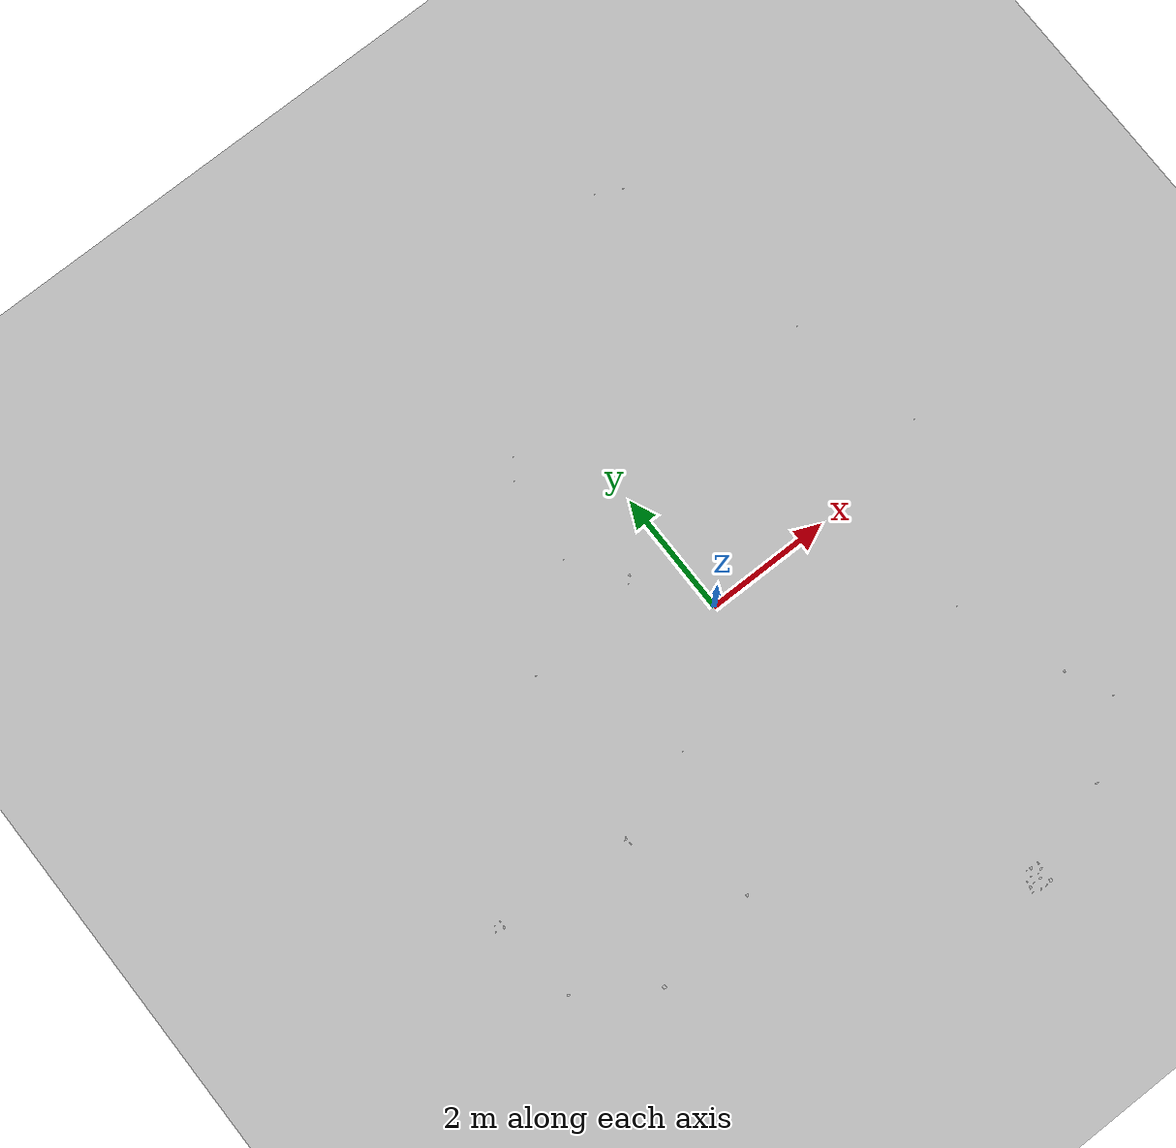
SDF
<sdf version="1.6">
 <world name="default">
  <model name="ground_plane">
   <static>1</static>
   <link name="link">
    <collision name="collision">
     <geometry><plane><normal>0 0 1</normal><size>100 100</size></plane></geometry>
     <surface><friction><ode><mu>100</mu><mu2>50</mu2></ode></friction></surface>
    </collision>
    <visual name="visual">
     <cast_shadows>0</cast_shadows>
     <geometry><plane><normal>0 0 1</normal><size>100 100</size></plane></geometry>
     <material>
      <script><uri>file://media/materials/scripts/gazebo.material</uri><name>Gazebo/Grey</name></script>
     </material>
    </visual>
   </link>
  </model>
  <light name="sun" type="directional">
   <pose>0 0 10 0 -0 0</pose>
   <diffuse>0.8 0.8 0.8 1</diffuse>
   <specular>0.1 0.1 0.1 1</specular>
   <attenuation>
    <range>1000</range>
    <constant>0.9</constant>
    <linear>0.01</linear>
    <quadratic>0.001</quadratic>
   </attenuation>
   <direction>-0.5 0.5 -1</direction>
  </light>
  <plugin name="SetupWorld" filename="libgazebo_plugins.so"/>
  <gravity>0 0 -9.8</gravity>
  <magnetic_field>6e-06 2.3e-05 -4.2e-05</magnetic_field>
  <atmosphere type="adiabatic"/>
  <physics name="default_physics" default="0" type="ode">
   <max_step_size>0.001</max_step_size>
   <real_time_factor>1</real_time_factor>
   <real_time_update_rate>1000</real_time_update_rate>
  </physics>
  <scene><ambient>0.4 0.4 0.4 1</ambient><background>0.7 0.7 0.7 1</background><shadows>1</shadows></scene>
  <spherical_coordinates>
   <surface_model>EARTH_WGS84</surface_model>
   <latitude_deg>0</latitude_deg>
   <longitude_deg>0</longitude_deg>
   <elevation>0</elevation>
   <heading_deg>0</heading_deg>
  </spherical_coordinates>
  <model name="at0">
   <static>0</static>
   <link name="link">
    <inertial>
     <mass>0.01</mass>
     <inertia><ixx>4e-05</ixx><ixy>0</ixy><ixz>0</ixz><iyy>4e-05</iyy><iyz>0</iyz><izz>4e-05</izz></inertia>
    </inertial>
    <visual name="visual">
     <geometry><box><size>0.05 0.05 0.05</size></box></geometry>
     <material>
      <script>
       <uri>model://at0/materials/scripts</uri>
       <uri>model://at0/materials/textures</uri>
       <name>at0/Diffuse</name>
      </script>
     </material>
    </visual>
    <collision name="collision">
     <geometry><box><size>0.05 0.05 0.05</size></box></geometry>
     <surface><friction><ode><mu>0.8</mu><mu2>0.7</mu2></ode></friction></surface>
    </collision>
   </link>
   <pose>2.3606 5.72392 0.024997 2.9e-05 -2.9e-05 -1e-06</pose>
  </model>
  <model name="at1">
   <static>0</static>
   <link name="link">
    <inertial>
     <mass>0.01</mass>
     <inertia><ixx>4e-05</ixx><ixy>0</ixy><ixz>0</ixz><iyy>4e-05</iyy><iyz>0</iyz><izz>4e-05</izz></inertia>
    </inertial>
    <visual name="visual">
     <geometry><box><size>0.05 0.05 0.05</size></box></geometry>
     <material>
      <script>
       <uri>model://at0/materials/scripts</uri>
       <uri>model://at0/materials/textures</uri>
       <name>at0/Diffuse</name>
      </script>
     </material>
    </visual>
    <collision name="collision">
     <geometry><box><size>0.05 0.05 0.05</size></box></geometry>
     <surface><friction><ode><mu>0.8</mu><mu2>0.7</mu2></ode></friction></surface>
    </collision>
   </link>
   <pose>2.4606 5.72392 0.024997 2.9e-05 -2.9e-05 -1e-06</pose>
  </model>
  <model name="at2">
   <static>0</static>
   <link name="link">
    <inertial>
     <mass>0.01</mass>
     <inertia><ixx>4e-05</ixx><ixy>0</ixy><ixz>0</ixz><iyy>4e-05</iyy><iyz>0</iyz><izz>4e-05</izz></inertia>
    </inertial>
    <visual name="visual">
     <geometry><box><size>0.05 0.05 0.05</size></box></geometry>
     <material>
      <script>
       <uri>model://at0/materials/scripts</uri>
       <uri>model://at0/materials/textures</uri>
       <name>at0/Diffuse</name>
      </script>
     </material>
    </visual>
    <collision name="collision">
     <geometry><box><size>0.05 0.05 0.05</size></box></geometry>
     <surface><friction><ode><mu>0.8</mu><mu2>0.7</mu2></ode></friction></surface>
    </collision>
   </link>
   <pose>2.5606 5.72392 0.024997 2.9e-05 -2.9e-05 -1e-06</pose>
  </model>
  <model name="at3">
   <static>0</static>
   <link name="link">
    <inertial>
     <mass>0.01</mass>
     <inertia><ixx>4e-05</ixx><ixy>0</ixy><ixz>0</ixz><iyy>4e-05</iyy><iyz>0</iyz><izz>4e-05</izz></inertia>
    </inertial>
    <visual name="visual">
     <geometry><box><size>0.05 0.05 0.05</size></box></geometry>
     <material>
      <script>
       <uri>model://at0/materials/scripts</uri>
       <uri>model://at0/materials/textures</uri>
       <name>at0/Diffuse</name>
      </script>
     </material>
    </visual>
    <collision name="collision">
     <geometry><box><size>0.05 0.05 0.05</size></box></geometry>
     <surface><friction><ode><mu>0.8</mu><mu2>0.7</mu2></ode></friction></surface>
    </collision>
   </link>
   <pose>2.6606 5.72392 0.024997 2.9e-05 -2.9e-05 -1e-06</pose>
  </model>
  <model name="at4">
   <static>0</static>
   <link name="link">
    <inertial>
     <mass>0.01</mass>
     <inertia><ixx>4e-05</ixx><ixy>0</ixy><ixz>0</ixz><iyy>4e-05</iyy><iyz>0</iyz><izz>4e-05</izz></inertia>
    </inertial>
    <visual name="visual">
     <geometry><box><size>0.05 0.05 0.05</size></box></geometry>
     <material>
      <script>
       <uri>model://at0/materials/scripts</uri>
       <uri>model://at0/materials/textures</uri>
       <name>at0/Diffuse</name>
      </script>
     </material>
    </visual>
    <collision name="collision">
     <geometry><box><size>0.05 0.05 0.05</size></box></geometry>
     <surface><friction><ode><mu>0.8</mu><mu2>0.7</mu2></ode></friction></surface>
    </collision>
   </link>
   <pose>2.7606 5.72392 0.024997 2.9e-05 -2.9e-05 -1e-06</pose>
  </model>
  <model name="at5">
   <static>0</static>
   <link name="link">
    <inertial>
     <mass>0.01</mass>
     <inertia><ixx>4e-05</ixx><ixy>0</ixy><ixz>0</ixz><iyy>4e-05</iyy><iyz>0</iyz><izz>4e-05</izz></inertia>
    </inertial>
    <visual name="visual">
     <geometry><box><size>0.05 0.05 0.05</size></box></geometry>
     <material>
      <script>
       <uri>model://at0/materials/scripts</uri>
       <uri>model://at0/materials/textures</uri>
       <name>at0/Diffuse</name>
      </script>
     </material>
    </visual>
    <collision name="collision">
     <geometry><box><size>0.05 0.05 0.05</size></box></geometry>
     <surface><friction><ode><mu>0.8</mu><mu2>0.7</mu2></ode></friction></surface>
    </collision>
   </link>
   <pose>2.8606 5.72392 0.024997 2.9e-05 -2.9e-05 -1e-06</pose>
  </model>
  <model name="at6">
   <static>0</static>
   <link name="link">
    <inertial>
     <mass>0.01</mass>
     <inertia><ixx>4e-05</ixx><ixy>0</ixy><ixz>0</ixz><iyy>4e-05</iyy><iyz>0</iyz><izz>4e-05</izz></inertia>
    </inertial>
    <visual name="visual">
     <geometry><box><size>0.05 0.05 0.05</size></box></geometry>
     <material>
      <script>
       <uri>model://at0/materials/scripts</uri>
       <uri>model://at0/materials/textures</uri>
       <name>at0/Diffuse</name>
      </script>
     </material>
    </visual>
    <collision name="collision">
     <geometry><box><size>0.05 0.05 0.05</size></box></geometry>
     <surface><friction><ode><mu>0.8</mu><mu2>0.7</mu2></ode></friction></surface>
    </collision>
   </link>
   <pose>2.9606 5.72392 0.024997 2.9e-05 -2.9e-05 -1e-06</pose>
  </model>
  <model name="at7">
   <static>0</static>
   <link name="link">
    <inertial>
     <mass>0.01</mass>
     <inertia><ixx>4e-05</ixx><ixy>0</ixy><ixz>0</ixz><iyy>4e-05</iyy><iyz>0</iyz><izz>4e-05</izz></inertia>
    </inertial>
    <visual name="visual">
     <geometry><box><size>0.05 0.05 0.05</size></box></geometry>
     <material>
      <script>
       <uri>model://at0/materials/scripts</uri>
       <uri>model://at0/materials/textures</uri>
       <name>at0/Diffuse</name>
      </script>
     </material>
    </visual>
    <collision name="collision">
     <geometry><box><size>0.05 0.05 0.05</size></box></geometry>
     <surface><friction><ode><mu>0.8</mu><mu2>0.7</mu2></ode></friction></surface>
    </collision>
   </link>
   <pose>3.0606 5.72392 0.024997 2.9e-05 -2.9e-05 -1e-06</pose>
  </model>
  <model name="at8">
   <static>0</static>
   <link name="link">
    <inertial>
     <mass>0.01</mass>
     <inertia><ixx>4e-05</ixx><ixy>0</ixy><ixz>0</ixz><iyy>4e-05</iyy><iyz>0</iyz><izz>4e-05</izz></inertia>
    </inertial>
    <visual name="visual">
     <geometry><box><size>0.05 0.05 0.05</size></box></geometry>
     <material>
      <script>
       <uri>model://at0/materials/scripts</uri>
       <uri>model://at0/materials/textures</uri>
       <name>at0/Diffuse</name>
      </script>
     </material>
    </visual>
    <collision name="collision">
     <geometry><box><size>0.05 0.05 0.05</size></box></geometry>
     <surface><friction><ode><mu>0.8</mu><mu2>0.7</mu2></ode></friction></surface>
    </collision>
   </link>
   <pose>2.3606 5.82392 0.024997 2.9e-05 -2.9e-05 -1e-06</pose>
  </model>
  <model name="at9">
   <static>0</static>
   <link name="link">
    <inertial>
     <mass>0.01</mass>
     <inertia><ixx>4e-05</ixx><ixy>0</ixy><ixz>0</ixz><iyy>4e-05</iyy><iyz>0</iyz><izz>4e-05</izz></inertia>
    </inertial>
    <visual name="visual">
     <geometry><box><size>0.05 0.05 0.05</size></box></geometry>
     <material>
      <script>
       <uri>model://at0/materials/scripts</uri>
       <uri>model://at0/materials/textures</uri>
       <name>at0/Diffuse</name>
      </script>
     </material>
    </visual>
    <collision name="collision">
     <geometry><box><size>0.05 0.05 0.05</size></box></geometry>
     <surface><friction><ode><mu>0.8</mu><mu2>0.7</mu2></ode></friction></surface>
    </collision>
   </link>
   <pose>2.4606 5.82392 0.024997 2.9e-05 -2.9e-05 -1e-06</pose>
  </model>
  <model name="at10">
   <static>0</static>
   <link name="link">
    <inertial>
     <mass>0.01</mass>
     <inertia><ixx>4e-05</ixx><ixy>0</ixy><ixz>0</ixz><iyy>4e-05</iyy><iyz>0</iyz><izz>4e-05</izz></inertia>
    </inertial>
    <visual name="visual">
     <geometry><box><size>0.05 0.05 0.05</size></box></geometry>
     <material>
      <script>
       <uri>model://at0/materials/scripts</uri>
       <uri>model://at0/materials/textures</uri>
       <name>at0/Diffuse</name>
      </script>
     </material>
    </visual>
    <collision name="collision">
     <geometry><box><size>0.05 0.05 0.05</size></box></geometry>
     <surface><friction><ode><mu>0.8</mu><mu2>0.7</mu2></ode></friction></surface>
    </collision>
   </link>
   <pose>2.5606 5.82392 0.024997 2.9e-05 -2.9e-05 -1e-06</pose>
  </model>
  <model name="at11">
   <static>0</static>
   <link name="link">
    <inertial>
     <mass>0.01</mass>
     <inertia><ixx>4e-05</ixx><ixy>0</ixy><ixz>0</ixz><iyy>4e-05</iyy><iyz>0</iyz><izz>4e-05</izz></inertia>
    </inertial>
    <visual name="visual">
     <geometry><box><size>0.05 0.05 0.05</size></box></geometry>
     <material>
      <script>
       <uri>model://at0/materials/scripts</uri>
       <uri>model://at0/materials/textures</uri>
       <name>at0/Diffuse</name>
      </script>
     </material>
    </visual>
    <collision name="collision">
     <geometry><box><size>0.05 0.05 0.05</size></box></geometry>
     <surface><friction><ode><mu>0.8</mu><mu2>0.7</mu2></ode></friction></surface>
    </collision>
   </link>
   <pose>2.6606 5.82392 0.024997 2.9e-05 -2.9e-05 -1e-06</pose>
  </model>
  <model name="at12">
   <static>0</static>
   <link name="link">
    <inertial>
     <mass>0.01</mass>
     <inertia><ixx>4e-05</ixx><ixy>0</ixy><ixz>0</ixz><iyy>4e-05</iyy><iyz>0</iyz><izz>4e-05</izz></inertia>
    </inertial>
    <visual name="visual">
     <geometry><box><size>0.05 0.05 0.05</size></box></geometry>
     <material>
      <script>
       <uri>model://at0/materials/scripts</uri>
       <uri>model://at0/materials/textures</uri>
       <name>at0/Diffuse</name>
      </script>
     </material>
    </visual>
    <collision name="collision">
     <geometry><box><size>0.05 0.05 0.05</size></box></geometry>
     <surface><friction><ode><mu>0.8</mu><mu2>0.7</mu2></ode></friction></surface>
    </collision>
   </link>
   <pose>2.7606 5.82392 0.024997 2.9e-05 -2.9e-05 -1e-06</pose>
  </model>
  <model name="at13">
   <static>0</static>
   <link name="link">
    <inertial>
     <mass>0.01</mass>
     <inertia><ixx>4e-05</ixx><ixy>0</ixy><ixz>0</ixz><iyy>4e-05</iyy><iyz>0</iyz><izz>4e-05</izz></inertia>
    </inertial>
    <visual name="visual">
     <geometry><box><size>0.05 0.05 0.05</size></box></geometry>
     <material>
      <script>
       <uri>model://at0/materials/scripts</uri>
       <uri>model://at0/materials/textures</uri>
       <name>at0/Diffuse</name>
      </script>
     </material>
    </visual>
    <collision name="collision">
     <geometry><box><size>0.05 0.05 0.05</size></box></geometry>
     <surface><friction><ode><mu>0.8</mu><mu2>0.7</mu2></ode></friction></surface>
    </collision>
   </link>
   <pose>2.8606 5.82392 0.024997 2.9e-05 -2.9e-05 -1e-06</pose>
  </model>
  <model name="at14">
   <static>0</static>
   <link name="link">
    <inertial>
     <mass>0.01</mass>
     <inertia><ixx>4e-05</ixx><ixy>0</ixy><ixz>0</ixz><iyy>4e-05</iyy><iyz>0</iyz><izz>4e-05</izz></inertia>
    </inertial>
    <visual name="visual">
     <geometry><box><size>0.05 0.05 0.05</size></box></geometry>
     <material>
      <script>
       <uri>model://at0/materials/scripts</uri>
       <uri>model://at0/materials/textures</uri>
       <name>at0/Diffuse</name>
      </script>
     </material>
    </visual>
    <collision name="collision">
     <geometry><box><size>0.05 0.05 0.05</size></box></geometry>
     <surface><friction><ode><mu>0.8</mu><mu2>0.7</mu2></ode></friction></surface>
    </collision>
   </link>
   <pose>2.9606 5.82392 0.024997 2.9e-05 -2.9e-05 -1e-06</pose>
  </model>
  <model name="at15">
   <static>0</static>
   <link name="link">
    <inertial>
     <mass>0.01</mass>
     <inertia><ixx>4e-05</ixx><ixy>0</ixy><ixz>0</ixz><iyy>4e-05</iyy><iyz>0</iyz><izz>4e-05</izz></inertia>
    </inertial>
    <visual name="visual">
     <geometry><box><size>0.05 0.05 0.05</size></box></geometry>
     <material>
      <script>
       <uri>model://at0/materials/scripts</uri>
       <uri>model://at0/materials/textures</uri>
       <name>at0/Diffuse</name>
      </script>
     </material>
    </visual>
    <collision name="collision">
     <geometry><box><size>0.05 0.05 0.05</size></box></geometry>
     <surface><friction><ode><mu>0.8</mu><mu2>0.7</mu2></ode></friction></surface>
    </collision>
   </link>
   <pose>3.0606 5.82392 0.024997 2.9e-05 -2.9e-05 -1e-06</pose>
  </model>
  <model name="at16">
   <static>0</static>
   <link name="link">
    <inertial>
     <mass>0.01</mass>
     <inertia><ixx>4e-05</ixx><ixy>0</ixy><ixz>0</ixz><iyy>4e-05</iyy><iyz>0</iyz><izz>4e-05</izz></inertia>
    </inertial>
    <visual name="visual">
     <geometry><box><size>0.05 0.05 0.05</size></box></geometry>
     <material>
      <script>
       <uri>model://at0/materials/scripts</uri>
       <uri>model://at0/materials/textures</uri>
       <name>at0/Diffuse</name>
      </script>
     </material>
    </visual>
    <collision name="collision">
     <geometry><box><size>0.05 0.05 0.05</size></box></geometry>
     <surface><friction><ode><mu>0.8</mu><mu2>0.7</mu2></ode></friction></surface>
    </collision>
   </link>
   <pose>2.3606 5.92392 0.024997 2.9e-05 -2.9e-05 -1e-06</pose>
  </model>
  <model name="at17">
   <static>0</static>
   <link name="link">
    <inertial>
     <mass>0.01</mass>
     <inertia><ixx>4e-05</ixx><ixy>0</ixy><ixz>0</ixz><iyy>4e-05</iyy><iyz>0</iyz><izz>4e-05</izz></inertia>
    </inertial>
    <visual name="visual">
     <geometry><box><size>0.05 0.05 0.05</size></box></geometry>
     <material>
      <script>
       <uri>model://at0/materials/scripts</uri>
       <uri>model://at0/materials/textures</uri>
       <name>at0/Diffuse</name>
      </script>
     </material>
    </visual>
    <collision name="collision">
     <geometry><box><size>0.05 0.05 0.05</size></box></geometry>
     <surface><friction><ode><mu>0.8</mu><mu2>0.7</mu2></ode></friction></surface>
    </collision>
   </link>
   <pose>2.4606 5.92392 0.024997 2.9e-05 -2.9e-05 -1e-06</pose>
  </model>
  <model name="at18">
   <static>0</static>
   <link name="link">
    <inertial>
     <mass>0.01</mass>
     <inertia><ixx>4e-05</ixx><ixy>0</ixy><ixz>0</ixz><iyy>4e-05</iyy><iyz>0</iyz><izz>4e-05</izz></inertia>
    </inertial>
    <visual name="visual">
     <geometry><box><size>0.05 0.05 0.05</size></box></geometry>
     <material>
      <script>
       <uri>model://at0/materials/scripts</uri>
       <uri>model://at0/materials/textures</uri>
       <name>at0/Diffuse</name>
      </script>
     </material>
    </visual>
    <collision name="collision">
     <geometry><box><size>0.05 0.05 0.05</size></box></geometry>
     <surface><friction><ode><mu>0.8</mu><mu2>0.7</mu2></ode></friction></surface>
    </collision>
   </link>
   <pose>2.5606 5.92392 0.024997 2.9e-05 -2.9e-05 -1e-06</pose>
  </model>
  <model name="at19">
   <static>0</static>
   <link name="link">
    <inertial>
     <mass>0.01</mass>
     <inertia><ixx>4e-05</ixx><ixy>0</ixy><ixz>0</ixz><iyy>4e-05</iyy><iyz>0</iyz><izz>4e-05</izz></inertia>
    </inertial>
    <visual name="visual">
     <geometry><box><size>0.05 0.05 0.05</size></box></geometry>
     <material>
      <script>
       <uri>model://at0/materials/scripts</uri>
       <uri>model://at0/materials/textures</uri>
       <name>at0/Diffuse</name>
      </script>
     </material>
    </visual>
    <collision name="collision">
     <geometry><box><size>0.05 0.05 0.05</size></box></geometry>
     <surface><friction><ode><mu>0.8</mu><mu2>0.7</mu2></ode></friction></surface>
    </collision>
   </link>
   <pose>2.6606 5.92392 0.024997 2.9e-05 -2.9e-05 -1e-06</pose>
  </model>
  <model name="at20">
   <static>0</static>
   <link name="link">
    <inertial>
     <mass>0.01</mass>
     <inertia><ixx>4e-05</ixx><ixy>0</ixy><ixz>0</ixz><iyy>4e-05</iyy><iyz>0</iyz><izz>4e-05</izz></inertia>
    </inertial>
    <visual name="visual">
     <geometry><box><size>0.05 0.05 0.05</size></box></geometry>
     <material>
      <script>
       <uri>model://at0/materials/scripts</uri>
       <uri>model://at0/materials/textures</uri>
       <name>at0/Diffuse</name>
      </script>
     </material>
    </visual>
    <collision name="collision">
     <geometry><box><size>0.05 0.05 0.05</size></box></geometry>
     <surface><friction><ode><mu>0.8</mu><mu2>0.7</mu2></ode></friction></surface>
    </collision>
   </link>
   <pose>2.7606 5.92392 0.024997 2.9e-05 -2.9e-05 -1e-06</pose>
  </model>
  <model name="at21">
   <static>0</static>
   <link name="link">
    <inertial>
     <mass>0.01</mass>
     <inertia><ixx>4e-05</ixx><ixy>0</ixy><ixz>0</ixz><iyy>4e-05</iyy><iyz>0</iyz><izz>4e-05</izz></inertia>
    </inertial>
    <visual name="visual">
     <geometry><box><size>0.05 0.05 0.05</size></box></geometry>
     <material>
      <script>
       <uri>model://at0/materials/scripts</uri>
       <uri>model://at0/materials/textures</uri>
       <name>at0/Diffuse</name>
      </script>
     </material>
    </visual>
    <collision name="collision">
     <geometry><box><size>0.05 0.05 0.05</size></box></geometry>
     <surface><friction><ode><mu>0.8</mu><mu2>0.7</mu2></ode></friction></surface>
    </collision>
   </link>
   <pose>2.8606 5.92392 0.024997 2.9e-05 -2.9e-05 -1e-06</pose>
  </model>
  <model name="at22">
   <static>0</static>
   <link name="link">
    <inertial>
     <mass>0.01</mass>
     <inertia><ixx>4e-05</ixx><ixy>0</ixy><ixz>0</ixz><iyy>4e-05</iyy><iyz>0</iyz><izz>4e-05</izz></inertia>
    </inertial>
    <visual name="visual">
     <geometry><box><size>0.05 0.05 0.05</size></box></geometry>
     <material>
      <script>
       <uri>model://at0/materials/scripts</uri>
       <uri>model://at0/materials/textures</uri>
       <name>at0/Diffuse</name>
      </script>
     </material>
    </visual>
    <collision name="collision">
     <geometry><box><size>0.05 0.05 0.05</size></box></geometry>
     <surface><friction><ode><mu>0.8</mu><mu2>0.7</mu2></ode></friction></surface>
    </collision>
   </link>
   <pose>2.9606 5.92392 0.024997 2.9e-05 -2.9e-05 -1e-06</pose>
  </model>
  <model name="at23">
   <static>0</static>
   <link name="link">
    <inertial>
     <mass>0.01</mass>
     <inertia><ixx>4e-05</ixx><ixy>0</ixy><ixz>0</ixz><iyy>4e-05</iyy><iyz>0</iyz><izz>4e-05</izz></inertia>
    </inertial>
    <visual name="visual">
     <geometry><box><size>0.05 0.05 0.05</size></box></geometry>
     <material>
      <script>
       <uri>model://at0/materials/scripts</uri>
       <uri>model://at0/materials/textures</uri>
       <name>at0/Diffuse</name>
      </script>
     </material>
    </visual>
    <collision name="collision">
     <geometry><box><size>0.05 0.05 0.05</size></box></geometry>
     <surface><friction><ode><mu>0.8</mu><mu2>0.7</mu2></ode></friction></surface>
    </collision>
   </link>
   <pose>3.0606 5.92392 0.024997 2.9e-05 -2.9e-05 -1e-06</pose>
  </model>
  <model name="at24">
   <static>0</static>
   <link name="link">
    <inertial>
     <mass>0.01</mass>
     <inertia><ixx>4e-05</ixx><ixy>0</ixy><ixz>0</ixz><iyy>4e-05</iyy><iyz>0</iyz><izz>4e-05</izz></inertia>
    </inertial>
    <visual name="visual">
     <geometry><box><size>0.05 0.05 0.05</size></box></geometry>
     <material>
      <script>
       <uri>model://at0/materials/scripts</uri>
       <uri>model://at0/materials/textures</uri>
       <name>at0/Diffuse</name>
      </script>
     </material>
    </visual>
    <collision name="collision">
     <geometry><box><size>0.05 0.05 0.05</size></box></geometry>
     <surface><friction><ode><mu>0.8</mu><mu2>0.7</mu2></ode></friction></surface>
    </collision>
   </link>
   <pose>2.3606 6.02392 0.024997 2.9e-05 -2.9e-05 -1e-06</pose>
  </model>
  <model name="at25">
   <static>0</static>
   <link name="link">
    <inertial>
     <mass>0.01</mass>
     <inertia><ixx>4e-05</ixx><ixy>0</ixy><ixz>0</ixz><iyy>4e-05</iyy><iyz>0</iyz><izz>4e-05</izz></inertia>
    </inertial>
    <visual name="visual">
     <geometry><box><size>0.05 0.05 0.05</size></box></geometry>
     <material>
      <script>
       <uri>model://at0/materials/scripts</uri>
       <uri>model://at0/materials/textures</uri>
       <name>at0/Diffuse</name>
      </script>
     </material>
    </visual>
    <collision name="collision">
     <geometry><box><size>0.05 0.05 0.05</size></box></geometry>
     <surface><friction><ode><mu>0.8</mu><mu2>0.7</mu2></ode></friction></surface>
    </collision>
   </link>
   <pose>2.4606 6.02392 0.024997 2.9e-05 -2.9e-05 -1e-06</pose>
  </model>
  <model name="at26">
   <static>0</static>
   <link name="link">
    <inertial>
     <mass>0.01</mass>
     <inertia><ixx>4e-05</ixx><ixy>0</ixy><ixz>0</ixz><iyy>4e-05</iyy><iyz>0</iyz><izz>4e-05</izz></inertia>
    </inertial>
    <visual name="visual">
     <geometry><box><size>0.05 0.05 0.05</size></box></geometry>
     <material>
      <script>
       <uri>model://at0/materials/scripts</uri>
       <uri>model://at0/materials/textures</uri>
       <name>at0/Diffuse</name>
      </script>
     </material>
    </visual>
    <collision name="collision">
     <geometry><box><size>0.05 0.05 0.05</size></box></geometry>
     <surface><friction><ode><mu>0.8</mu><mu2>0.7</mu2></ode></friction></surface>
    </collision>
   </link>
   <pose>2.5606 6.02392 0.024997 2.9e-05 -2.9e-05 -1e-06</pose>
  </model>
  <model name="at27">
   <static>0</static>
   <link name="link">
    <inertial>
     <mass>0.01</mass>
     <inertia><ixx>4e-05</ixx><ixy>0</ixy><ixz>0</ixz><iyy>4e-05</iyy><iyz>0</iyz><izz>4e-05</izz></inertia>
    </inertial>
    <visual name="visual">
     <geometry><box><size>0.05 0.05 0.05</size></box></geometry>
     <material>
      <script>
       <uri>model://at0/materials/scripts</uri>
       <uri>model://at0/materials/textures</uri>
       <name>at0/Diffuse</name>
      </script>
     </material>
    </visual>
    <collision name="collision">
     <geometry><box><size>0.05 0.05 0.05</size></box></geometry>
     <surface><friction><ode><mu>0.8</mu><mu2>0.7</mu2></ode></friction></surface>
    </collision>
   </link>
   <pose>2.6606 6.02392 0.024997 2.9e-05 -2.9e-05 -1e-06</pose>
  </model>
  <model name="at28">
   <static>0</static>
   <link name="link">
    <inertial>
     <mass>0.01</mass>
     <inertia><ixx>4e-05</ixx><ixy>0</ixy><ixz>0</ixz><iyy>4e-05</iyy><iyz>0</iyz><izz>4e-05</izz></inertia>
    </inertial>
    <visual name="visual">
     <geometry><box><size>0.05 0.05 0.05</size></box></geometry>
     <material>
      <script>
       <uri>model://at0/materials/scripts</uri>
       <uri>model://at0/materials/textures</uri>
       <name>at0/Diffuse</name>
      </script>
     </material>
    </visual>
    <collision name="collision">
     <geometry><box><size>0.05 0.05 0.05</size></box></geometry>
     <surface><friction><ode><mu>0.8</mu><mu2>0.7</mu2></ode></friction></surface>
    </collision>
   </link>
   <pose>2.7606 6.02392 0.024997 2.9e-05 -2.9e-05 -1e-06</pose>
  </model>
  <model name="at29">
   <static>0</static>
   <link name="link">
    <inertial>
     <mass>0.01</mass>
     <inertia><ixx>4e-05</ixx><ixy>0</ixy><ixz>0</ixz><iyy>4e-05</iyy><iyz>0</iyz><izz>4e-05</izz></inertia>
    </inertial>
    <visual name="visual">
     <geometry><box><size>0.05 0.05 0.05</size></box></geometry>
     <material>
      <script>
       <uri>model://at0/materials/scripts</uri>
       <uri>model://at0/materials/textures</uri>
       <name>at0/Diffuse</name>
      </script>
     </material>
    </visual>
    <collision name="collision">
     <geometry><box><size>0.05 0.05 0.05</size></box></geometry>
     <surface><friction><ode><mu>0.8</mu><mu2>0.7</mu2></ode></friction></surface>
    </collision>
   </link>
   <pose>2.8606 6.02392 0.024997 2.9e-05 -2.9e-05 -1e-06</pose>
  </model>
  <model name="at30">
   <static>0</static>
   <link name="link">
    <inertial>
     <mass>0.01</mass>
     <inertia><ixx>4e-05</ixx><ixy>0</ixy><ixz>0</ixz><iyy>4e-05</iyy><iyz>0</iyz><izz>4e-05</izz></inertia>
    </inertial>
    <visual name="visual">
     <geometry><box><size>0.05 0.05 0.05</size></box></geometry>
     <material>
      <script>
       <uri>model://at0/materials/scripts</uri>
       <uri>model://at0/materials/textures</uri>
       <name>at0/Diffuse</name>
      </script>
     </material>
    </visual>
    <collision name="collision">
     <geometry><box><size>0.05 0.05 0.05</size></box></geometry>
     <surface><friction><ode><mu>0.8</mu><mu2>0.7</mu2></ode></friction></surface>
    </collision>
   </link>
   <pose>2.9606 6.02392 0.024997 2.9e-05 -2.9e-05 -1e-06</pose>
  </model>
  <model name="at31">
   <static>0</static>
   <link name="link">
    <inertial>
     <mass>0.01</mass>
     <inertia><ixx>4e-05</ixx><ixy>0</ixy><ixz>0</ixz><iyy>4e-05</iyy><iyz>0</iyz><izz>4e-05</izz></inertia>
    </inertial>
    <visual name="visual">
     <geometry><box><size>0.05 0.05 0.05</size></box></geometry>
     <material>
      <script>
       <uri>model://at0/materials/scripts</uri>
       <uri>model://at0/materials/textures</uri>
       <name>at0/Diffuse</name>
      </script>
     </material>
    </visual>
    <collision name="collision">
     <geometry><box><size>0.05 0.05 0.05</size></box></geometry>
     <surface><friction><ode><mu>0.8</mu><mu2>0.7</mu2></ode></friction></surface>
    </collision>
   </link>
   <pose>3.0606 6.02392 0.024997 2.9e-05 -2.9e-05 -1e-06</pose>
  </model>
  <model name="at32">
   <static>0</static>
   <link name="link">
    <inertial>
     <mass>0.01</mass>
     <inertia><ixx>4e-05</ixx><ixy>0</ixy><ixz>0</ixz><iyy>4e-05</iyy><iyz>0</iyz><izz>4e-05</izz></inertia>
    </inertial>
    <visual name="visual">
     <geometry><box><size>0.05 0.05 0.05</size></box></geometry>
     <material>
      <script>
       <uri>model://at0/materials/scripts</uri>
       <uri>model://at0/materials/textures</uri>
       <name>at0/Diffuse</name>
      </script>
     </material>
    </visual>
    <collision name="collision">
     <geometry><box><size>0.05 0.05 0.05</size></box></geometry>
     <surface><friction><ode><mu>0.8</mu><mu2>0.7</mu2></ode></friction></surface>
    </collision>
   </link>
   <pose>1.01741 -6.08293 0.024997 2.9e-05 -2.9e-05 -1e-06</pose>
  </model>
  <model name="at33">
   <static>0</static>
   <link name="link">
    <inertial>
     <mass>0.01</mass>
     <inertia><ixx>4e-05</ixx><ixy>0</ixy><ixz>0</ixz><iyy>4e-05</iyy><iyz>0</iyz><izz>4e-05</izz></inertia>
    </inertial>
    <visual name="visual">
     <geometry><box><size>0.05 0.05 0.05</size></box></geometry>
     <material>
      <script>
       <uri>model://at0/materials/scripts</uri>
       <uri>model://at0/materials/textures</uri>
       <name>at0/Diffuse</name>
      </script>
     </material>
    </visual>
    <collision name="collision">
     <geometry><box><size>0.05 0.05 0.05</size></box></geometry>
     <surface><friction><ode><mu>0.8</mu><mu2>0.7</mu2></ode></friction></surface>
    </collision>
   </link>
   <pose>1.11741 -6.08293 0.024997 2.9e-05 -2.9e-05 -1e-06</pose>
  </model>
  <model name="at34">
   <static>0</static>
   <link name="link">
    <inertial>
     <mass>0.01</mass>
     <inertia><ixx>4e-05</ixx><ixy>0</ixy><ixz>0</ixz><iyy>4e-05</iyy><iyz>0</iyz><izz>4e-05</izz></inertia>
    </inertial>
    <visual name="visual">
     <geometry><box><size>0.05 0.05 0.05</size></box></geometry>
     <material>
      <script>
       <uri>model://at0/materials/scripts</uri>
       <uri>model://at0/materials/textures</uri>
       <name>at0/Diffuse</name>
      </script>
     </material>
    </visual>
    <collision name="collision">
     <geometry><box><size>0.05 0.05 0.05</size></box></geometry>
     <surface><friction><ode><mu>0.8</mu><mu2>0.7</mu2></ode></friction></surface>
    </collision>
   </link>
   <pose>1.21741 -6.08293 0.024997 2.9e-05 -2.9e-05 -1e-06</pose>
  </model>
  <model name="at35">
   <static>0</static>
   <link name="link">
    <inertial>
     <mass>0.01</mass>
     <inertia><ixx>4e-05</ixx><ixy>0</ixy><ixz>0</ixz><iyy>4e-05</iyy><iyz>0</iyz><izz>4e-05</izz></inertia>
    </inertial>
    <visual name="visual">
     <geometry><box><size>0.05 0.05 0.05</size></box></geometry>
     <material>
      <script>
       <uri>model://at0/materials/scripts</uri>
       <uri>model://at0/materials/textures</uri>
       <name>at0/Diffuse</name>
      </script>
     </material>
    </visual>
    <collision name="collision">
     <geometry><box><size>0.05 0.05 0.05</size></box></geometry>
     <surface><friction><ode><mu>0.8</mu><mu2>0.7</mu2></ode></friction></surface>
    </collision>
   </link>
   <pose>1.31741 -6.08293 0.024997 2.9e-05 -2.9e-05 -1e-06</pose>
  </model>
  <model name="at36">
   <static>0</static>
   <link name="link">
    <inertial>
     <mass>0.01</mass>
     <inertia><ixx>4e-05</ixx><ixy>0</ixy><ixz>0</ixz><iyy>4e-05</iyy><iyz>0</iyz><izz>4e-05</izz></inertia>
    </inertial>
    <visual name="visual">
     <geometry><box><size>0.05 0.05 0.05</size></box></geometry>
     <material>
      <script>
       <uri>model://at0/materials/scripts</uri>
       <uri>model://at0/materials/textures</uri>
       <name>at0/Diffuse</name>
      </script>
     </material>
    </visual>
    <collision name="collision">
     <geometry><box><size>0.05 0.05 0.05</size></box></geometry>
     <surface><friction><ode><mu>0.8</mu><mu2>0.7</mu2></ode></friction></surface>
    </collision>
   </link>
   <pose>1.01741 -5.98293 0.024997 2.9e-05 -2.9e-05 -1e-06</pose>
  </model>
  <model name="at37">
   <static>0</static>
   <link name="link">
    <inertial>
     <mass>0.01</mass>
     <inertia><ixx>4e-05</ixx><ixy>0</ixy><ixz>0</ixz><iyy>4e-05</iyy><iyz>0</iyz><izz>4e-05</izz></inertia>
    </inertial>
    <visual name="visual">
     <geometry><box><size>0.05 0.05 0.05</size></box></geometry>
     <material>
      <script>
       <uri>model://at0/materials/scripts</uri>
       <uri>model://at0/materials/textures</uri>
       <name>at0/Diffuse</name>
      </script>
     </material>
    </visual>
    <collision name="collision">
     <geometry><box><size>0.05 0.05 0.05</size></box></geometry>
     <surface><friction><ode><mu>0.8</mu><mu2>0.7</mu2></ode></friction></surface>
    </collision>
   </link>
   <pose>1.11741 -5.98293 0.024997 2.9e-05 -2.9e-05 -1e-06</pose>
  </model>
  <model name="at38">
   <static>0</static>
   <link name="link">
    <inertial>
     <mass>0.01</mass>
     <inertia><ixx>4e-05</ixx><ixy>0</ixy><ixz>0</ixz><iyy>4e-05</iyy><iyz>0</iyz><izz>4e-05</izz></inertia>
    </inertial>
    <visual name="visual">
     <geometry><box><size>0.05 0.05 0.05</size></box></geometry>
     <material>
      <script>
       <uri>model://at0/materials/scripts</uri>
       <uri>model://at0/materials/textures</uri>
       <name>at0/Diffuse</name>
      </script>
     </material>
    </visual>
    <collision name="collision">
     <geometry><box><size>0.05 0.05 0.05</size></box></geometry>
     <surface><friction><ode><mu>0.8</mu><mu2>0.7</mu2></ode></friction></surface>
    </collision>
   </link>
   <pose>1.21741 -5.98293 0.024997 2.9e-05 -2.9e-05 -1e-06</pose>
  </model>
  <model name="at39">
   <static>0</static>
   <link name="link">
    <inertial>
     <mass>0.01</mass>
     <inertia><ixx>4e-05</ixx><ixy>0</ixy><ixz>0</ixz><iyy>4e-05</iyy><iyz>0</iyz><izz>4e-05</izz></inertia>
    </inertial>
    <visual name="visual">
     <geometry><box><size>0.05 0.05 0.05</size></box></geometry>
     <material>
      <script>
       <uri>model://at0/materials/scripts</uri>
       <uri>model://at0/materials/textures</uri>
       <name>at0/Diffuse</name>
      </script>
     </material>
    </visual>
    <collision name="collision">
     <geometry><box><size>0.05 0.05 0.05</size></box></geometry>
     <surface><friction><ode><mu>0.8</mu><mu2>0.7</mu2></ode></friction></surface>
    </collision>
   </link>
   <pose>1.31741 -5.98293 0.024997 2.9e-05 -2.9e-05 -1e-06</pose>
  </model>
  <model name="at40">
   <static>0</static>
   <link name="link">
    <inertial>
     <mass>0.01</mass>
     <inertia><ixx>4e-05</ixx><ixy>0</ixy><ixz>0</ixz><iyy>4e-05</iyy><iyz>0</iyz><izz>4e-05</izz></inertia>
    </inertial>
    <visual name="visual">
     <geometry><box><size>0.05 0.05 0.05</size></box></geometry>
     <material>
      <script>
       <uri>model://at0/materials/scripts</uri>
       <uri>model://at0/materials/textures</uri>
       <name>at0/Diffuse</name>
      </script>
     </material>
    </visual>
    <collision name="collision">
     <geometry><box><size>0.05 0.05 0.05</size></box></geometry>
     <surface><friction><ode><mu>0.8</mu><mu2>0.7</mu2></ode></friction></surface>
    </collision>
   </link>
   <pose>1.01741 -5.88293 0.024997 2.9e-05 -2.9e-05 -1e-06</pose>
  </model>
  <model name="at41">
   <static>0</static>
   <link name="link">
    <inertial>
     <mass>0.01</mass>
     <inertia><ixx>4e-05</ixx><ixy>0</ixy><ixz>0</ixz><iyy>4e-05</iyy><iyz>0</iyz><izz>4e-05</izz></inertia>
    </inertial>
    <visual name="visual">
     <geometry><box><size>0.05 0.05 0.05</size></box></geometry>
     <material>
      <script>
       <uri>model://at0/materials/scripts</uri>
       <uri>model://at0/materials/textures</uri>
       <name>at0/Diffuse</name>
      </script>
     </material>
    </visual>
    <collision name="collision">
     <geometry><box><size>0.05 0.05 0.05</size></box></geometry>
     <surface><friction><ode><mu>0.8</mu><mu2>0.7</mu2></ode></friction></surface>
    </collision>
   </link>
   <pose>1.11741 -5.88293 0.024997 2.9e-05 -2.9e-05 -1e-06</pose>
  </model>
  <model name="at42">
   <static>0</static>
   <link name="link">
    <inertial>
     <mass>0.01</mass>
     <inertia><ixx>4e-05</ixx><ixy>0</ixy><ixz>0</ixz><iyy>4e-05</iyy><iyz>0</iyz><izz>4e-05</izz></inertia>
    </inertial>
    <visual name="visual">
     <geometry><box><size>0.05 0.05 0.05</size></box></geometry>
     <material>
      <script>
       <uri>model://at0/materials/scripts</uri>
       <uri>model://at0/materials/textures</uri>
       <name>at0/Diffuse</name>
      </script>
     </material>
    </visual>
    <collision name="collision">
     <geometry><box><size>0.05 0.05 0.05</size></box></geometry>
     <surface><friction><ode><mu>0.8</mu><mu2>0.7</mu2></ode></friction></surface>
    </collision>
   </link>
   <pose>1.21741 -5.88293 0.024997 2.9e-05 -2.9e-05 -1e-06</pose>
  </model>
  <model name="at43">
   <static>0</static>
   <link name="link">
    <inertial>
     <mass>0.01</mass>
     <inertia><ixx>4e-05</ixx><ixy>0</ixy><ixz>0</ixz><iyy>4e-05</iyy><iyz>0</iyz><izz>4e-05</izz></inertia>
    </inertial>
    <visual name="visual">
     <geometry><box><size>0.05 0.05 0.05</size></box></geometry>
     <material>
      <script>
       <uri>model://at0/materials/scripts</uri>
       <uri>model://at0/materials/textures</uri>
       <name>at0/Diffuse</name>
      </script>
     </material>
    </visual>
    <collision name="collision">
     <geometry><box><size>0.05 0.05 0.05</size></box></geometry>
     <surface><friction><ode><mu>0.8</mu><mu2>0.7</mu2></ode></friction></surface>
    </collision>
   </link>
   <pose>1.31741 -5.88293 0.024997 2.9e-05 -2.9e-05 -1e-06</pose>
  </model>
  <model name="at44">
   <static>0</static>
   <link name="link">
    <inertial>
     <mass>0.01</mass>
     <inertia><ixx>4e-05</ixx><ixy>0</ixy><ixz>0</ixz><iyy>4e-05</iyy><iyz>0</iyz><izz>4e-05</izz></inertia>
    </inertial>
    <visual name="visual">
     <geometry><box><size>0.05 0.05 0.05</size></box></geometry>
     <material>
      <script>
       <uri>model://at0/materials/scripts</uri>
       <uri>model://at0/materials/textures</uri>
       <name>at0/Diffuse</name>
      </script>
     </material>
    </visual>
    <collision name="collision">
     <geometry><box><size>0.05 0.05 0.05</size></box></geometry>
     <surface><friction><ode><mu>0.8</mu><mu2>0.7</mu2></ode></friction></surface>
    </collision>
   </link>
   <pose>1.01741 -5.78293 0.024997 2.9e-05 -2.9e-05 -1e-06</pose>
  </model>
  <model name="at45">
   <static>0</static>
   <link name="link">
    <inertial>
     <mass>0.01</mass>
     <inertia><ixx>4e-05</ixx><ixy>0</ixy><ixz>0</ixz><iyy>4e-05</iyy><iyz>0</iyz><izz>4e-05</izz></inertia>
    </inertial>
    <visual name="visual">
     <geometry><box><size>0.05 0.05 0.05</size></box></geometry>
     <material>
      <script>
       <uri>model://at0/materials/scripts</uri>
       <uri>model://at0/materials/textures</uri>
       <name>at0/Diffuse</name>
      </script>
     </material>
    </visual>
    <collision name="collision">
     <geometry><box><size>0.05 0.05 0.05</size></box></geometry>
     <surface><friction><ode><mu>0.8</mu><mu2>0.7</mu2></ode></friction></surface>
    </collision>
   </link>
   <pose>1.11741 -5.78293 0.024997 2.9e-05 -2.9e-05 -1e-06</pose>
  </model>
  <model name="at46">
   <static>0</static>
   <link name="link">
    <inertial>
     <mass>0.01</mass>
     <inertia><ixx>4e-05</ixx><ixy>0</ixy><ixz>0</ixz><iyy>4e-05</iyy><iyz>0</iyz><izz>4e-05</izz></inertia>
    </inertial>
    <visual name="visual">
     <geometry><box><size>0.05 0.05 0.05</size></box></geometry>
     <material>
      <script>
       <uri>model://at0/materials/scripts</uri>
       <uri>model://at0/materials/textures</uri>
       <name>at0/Diffuse</name>
      </script>
     </material>
    </visual>
    <collision name="collision">
     <geometry><box><size>0.05 0.05 0.05</size></box></geometry>
     <surface><friction><ode><mu>0.8</mu><mu2>0.7</mu2></ode></friction></surface>
    </collision>
   </link>
   <pose>1.21741 -5.78293 0.024997 2.9e-05 -2.9e-05 -1e-06</pose>
  </model>
  <model name="at47">
   <static>0</static>
   <link name="link">
    <inertial>
     <mass>0.01</mass>
     <inertia><ixx>4e-05</ixx><ixy>0</ixy><ixz>0</ixz><iyy>4e-05</iyy><iyz>0</iyz><izz>4e-05</izz></inertia>
    </inertial>
    <visual name="visual">
     <geometry><box><size>0.05 0.05 0.05</size></box></geometry>
     <material>
      <script>
       <uri>model://at0/materials/scripts</uri>
       <uri>model://at0/materials/textures</uri>
       <name>at0/Diffuse</name>
      </script>
     </material>
    </visual>
    <collision name="collision">
     <geometry><box><size>0.05 0.05 0.05</size></box></geometry>
     <surface><friction><ode><mu>0.8</mu><mu2>0.7</mu2></ode></friction></surface>
    </collision>
   </link>
   <pose>1.31741 -5.78293 0.024997 2.9e-05 -2.9e-05 -1e-06</pose>
  </model>
  <model name="at48">
   <static>0</static>
   <link name="link">
    <inertial>
     <mass>0.01</mass>
     <inertia><ixx>4e-05</ixx><ixy>0</ixy><ixz>0</ixz><iyy>4e-05</iyy><iyz>0</iyz><izz>4e-05</izz></inertia>
    </inertial>
    <visual name="visual">
     <geometry><box><size>0.05 0.05 0.05</size></box></geometry>
     <material>
      <script>
       <uri>model://at0/materials/scripts</uri>
       <uri>model://at0/materials/textures</uri>
       <name>at0/Diffuse</name>
      </script>
     </material>
    </visual>
    <collision name="collision">
     <geometry><box><size>0.05 0.05 0.05</size></box></geometry>
     <surface><friction><ode><mu>0.8</mu><mu2>0.7</mu2></ode></friction></surface>
    </collision>
   </link>
   <pose>-1.16998 3.28354 0.024997 2.9e-05 -2.9e-05 -1e-06</pose>
  </model>
  <model name="at49">
   <static>0</static>
   <link name="link">
    <inertial>
     <mass>0.01</mass>
     <inertia><ixx>4e-05</ixx><ixy>0</ixy><ixz>0</ixz><iyy>4e-05</iyy><iyz>0</iyz><izz>4e-05</izz></inertia>
    </inertial>
    <visual name="visual">
     <geometry><box><size>0.05 0.05 0.05</size></box></geometry>
     <material>
      <script>
       <uri>model://at0/materials/scripts</uri>
       <uri>model://at0/materials/textures</uri>
       <name>at0/Diffuse</name>
      </script>
     </material>
    </visual>
    <collision name="collision">
     <geometry><box><size>0.05 0.05 0.05</size></box></geometry>
     <surface><friction><ode><mu>0.8</mu><mu2>0.7</mu2></ode></friction></surface>
    </collision>
   </link>
   <pose>-1.06998 3.28354 0.024997 2.9e-05 -2.9e-05 -1e-06</pose>
  </model>
  <model name="at50">
   <static>0</static>
   <link name="link">
    <inertial>
     <mass>0.01</mass>
     <inertia><ixx>4e-05</ixx><ixy>0</ixy><ixz>0</ixz><iyy>4e-05</iyy><iyz>0</iyz><izz>4e-05</izz></inertia>
    </inertial>
    <visual name="visual">
     <geometry><box><size>0.05 0.05 0.05</size></box></geometry>
     <material>
      <script>
       <uri>model://at0/materials/scripts</uri>
       <uri>model://at0/materials/textures</uri>
       <name>at0/Diffuse</name>
      </script>
     </material>
    </visual>
    <collision name="collision">
     <geometry><box><size>0.05 0.05 0.05</size></box></geometry>
     <surface><friction><ode><mu>0.8</mu><mu2>0.7</mu2></ode></friction></surface>
    </collision>
   </link>
   <pose>-0.969985 3.28354 0.024997 2.9e-05 -2.9e-05 -1e-06</pose>
  </model>
  <model name="at51">
   <static>0</static>
   <link name="link">
    <inertial>
     <mass>0.01</mass>
     <inertia><ixx>4e-05</ixx><ixy>0</ixy><ixz>0</ixz><iyy>4e-05</iyy><iyz>0</iyz><izz>4e-05</izz></inertia>
    </inertial>
    <visual name="visual">
     <geometry><box><size>0.05 0.05 0.05</size></box></geometry>
     <material>
      <script>
       <uri>model://at0/materials/scripts</uri>
       <uri>model://at0/materials/textures</uri>
       <name>at0/Diffuse</name>
      </script>
     </material>
    </visual>
    <collision name="collision">
     <geometry><box><size>0.05 0.05 0.05</size></box></geometry>
     <surface><friction><ode><mu>0.8</mu><mu2>0.7</mu2></ode></friction></surface>
    </collision>
   </link>
   <pose>-0.869985 3.28354 0.024997 2.9e-05 -2.9e-05 -1e-06</pose>
  </model>
  <model name="at52">
   <static>0</static>
   <link name="link">
    <inertial>
     <mass>0.01</mass>
     <inertia><ixx>4e-05</ixx><ixy>0</ixy><ixz>0</ixz><iyy>4e-05</iyy><iyz>0</iyz><izz>4e-05</izz></inertia>
    </inertial>
    <visual name="visual">
     <geometry><box><size>0.05 0.05 0.05</size></box></geometry>
     <material>
      <script>
       <uri>model://at0/materials/scripts</uri>
       <uri>model://at0/materials/textures</uri>
       <name>at0/Diffuse</name>
      </script>
     </material>
    </visual>
    <collision name="collision">
     <geometry><box><size>0.05 0.05 0.05</size></box></geometry>
     <surface><friction><ode><mu>0.8</mu><mu2>0.7</mu2></ode></friction></surface>
    </collision>
   </link>
   <pose>-1.16998 3.38354 0.024997 2.9e-05 -2.9e-05 -1e-06</pose>
  </model>
  <model name="at53">
   <static>0</static>
   <link name="link">
    <inertial>
     <mass>0.01</mass>
     <inertia><ixx>4e-05</ixx><ixy>0</ixy><ixz>0</ixz><iyy>4e-05</iyy><iyz>0</iyz><izz>4e-05</izz></inertia>
    </inertial>
    <visual name="visual">
     <geometry><box><size>0.05 0.05 0.05</size></box></geometry>
     <material>
      <script>
       <uri>model://at0/materials/scripts</uri>
       <uri>model://at0/materials/textures</uri>
       <name>at0/Diffuse</name>
      </script>
     </material>
    </visual>
    <collision name="collision">
     <geometry><box><size>0.05 0.05 0.05</size></box></geometry>
     <surface><friction><ode><mu>0.8</mu><mu2>0.7</mu2></ode></friction></surface>
    </collision>
   </link>
   <pose>-1.06998 3.38354 0.024997 2.9e-05 -2.9e-05 -1e-06</pose>
  </model>
  <model name="at54">
   <static>0</static>
   <link name="link">
    <inertial>
     <mass>0.01</mass>
     <inertia><ixx>4e-05</ixx><ixy>0</ixy><ixz>0</ixz><iyy>4e-05</iyy><iyz>0</iyz><izz>4e-05</izz></inertia>
    </inertial>
    <visual name="visual">
     <geometry><box><size>0.05 0.05 0.05</size></box></geometry>
     <material>
      <script>
       <uri>model://at0/materials/scripts</uri>
       <uri>model://at0/materials/textures</uri>
       <name>at0/Diffuse</name>
      </script>
     </material>
    </visual>
    <collision name="collision">
     <geometry><box><size>0.05 0.05 0.05</size></box></geometry>
     <surface><friction><ode><mu>0.8</mu><mu2>0.7</mu2></ode></friction></surface>
    </collision>
   </link>
   <pose>-0.969985 3.38354 0.024997 2.9e-05 -2.9e-05 -1e-06</pose>
  </model>
  <model name="at55">
   <static>0</static>
   <link name="link">
    <inertial>
     <mass>0.01</mass>
     <inertia><ixx>4e-05</ixx><ixy>0</ixy><ixz>0</ixz><iyy>4e-05</iyy><iyz>0</iyz><izz>4e-05</izz></inertia>
    </inertial>
    <visual name="visual">
     <geometry><box><size>0.05 0.05 0.05</size></box></geometry>
     <material>
      <script>
       <uri>model://at0/materials/scripts</uri>
       <uri>model://at0/materials/textures</uri>
       <name>at0/Diffuse</name>
      </script>
     </material>
    </visual>
    <collision name="collision">
     <geometry><box><size>0.05 0.05 0.05</size></box></geometry>
     <surface><friction><ode><mu>0.8</mu><mu2>0.7</mu2></ode></friction></surface>
    </collision>
   </link>
   <pose>-0.869985 3.38354 0.024997 2.9e-05 -2.9e-05 -1e-06</pose>
  </model>
  <model name="at56">
   <static>0</static>
   <link name="link">
    <inertial>
     <mass>0.01</mass>
     <inertia><ixx>4e-05</ixx><ixy>0</ixy><ixz>0</ixz><iyy>4e-05</iyy><iyz>0</iyz><izz>4e-05</izz></inertia>
    </inertial>
    <visual name="visual">
     <geometry><box><size>0.05 0.05 0.05</size></box></geometry>
     <material>
      <script>
       <uri>model://at0/materials/scripts</uri>
       <uri>model://at0/materials/textures</uri>
       <name>at0/Diffuse</name>
      </script>
     </material>
    </visual>
    <collision name="collision">
     <geometry><box><size>0.05 0.05 0.05</size></box></geometry>
     <surface><friction><ode><mu>0.8</mu><mu2>0.7</mu2></ode></friction></surface>
    </collision>
   </link>
   <pose>-1.16998 3.48354 0.024997 2.9e-05 -2.9e-05 -1e-06</pose>
  </model>
  <model name="at57">
   <static>0</static>
   <link name="link">
    <inertial>
     <mass>0.01</mass>
     <inertia><ixx>4e-05</ixx><ixy>0</ixy><ixz>0</ixz><iyy>4e-05</iyy><iyz>0</iyz><izz>4e-05</izz></inertia>
    </inertial>
    <visual name="visual">
     <geometry><box><size>0.05 0.05 0.05</size></box></geometry>
     <material>
      <script>
       <uri>model://at0/materials/scripts</uri>
       <uri>model://at0/materials/textures</uri>
       <name>at0/Diffuse</name>
      </script>
     </material>
    </visual>
    <collision name="collision">
     <geometry><box><size>0.05 0.05 0.05</size></box></geometry>
     <surface><friction><ode><mu>0.8</mu><mu2>0.7</mu2></ode></friction></surface>
    </collision>
   </link>
   <pose>-1.06998 3.48354 0.024997 2.9e-05 -2.9e-05 -1e-06</pose>
  </model>
  <model name="at58">
   <static>0</static>
   <link name="link">
    <inertial>
     <mass>0.01</mass>
     <inertia><ixx>4e-05</ixx><ixy>0</ixy><ixz>0</ixz><iyy>4e-05</iyy><iyz>0</iyz><izz>4e-05</izz></inertia>
    </inertial>
    <visual name="visual">
     <geometry><box><size>0.05 0.05 0.05</size></box></geometry>
     <material>
      <script>
       <uri>model://at0/materials/scripts</uri>
       <uri>model://at0/materials/textures</uri>
       <name>at0/Diffuse</name>
      </script>
     </material>
    </visual>
    <collision name="collision">
     <geometry><box><size>0.05 0.05 0.05</size></box></geometry>
     <surface><friction><ode><mu>0.8</mu><mu2>0.7</mu2></ode></friction></surface>
    </collision>
   </link>
   <pose>-0.969985 3.48354 0.024997 2.9e-05 -2.9e-05 -1e-06</pose>
  </model>
  <model name="at59">
   <static>0</static>
   <link name="link">
    <inertial>
     <mass>0.01</mass>
     <inertia><ixx>4e-05</ixx><ixy>0</ixy><ixz>0</ixz><iyy>4e-05</iyy><iyz>0</iyz><izz>4e-05</izz></inertia>
    </inertial>
    <visual name="visual">
     <geometry><box><size>0.05 0.05 0.05</size></box></geometry>
     <material>
      <script>
       <uri>model://at0/materials/scripts</uri>
       <uri>model://at0/materials/textures</uri>
       <name>at0/Diffuse</name>
      </script>
     </material>
    </visual>
    <collision name="collision">
     <geometry><box><size>0.05 0.05 0.05</size></box></geometry>
     <surface><friction><ode><mu>0.8</mu><mu2>0.7</mu2></ode></friction></surface>
    </collision>
   </link>
   <pose>-0.869985 3.48354 0.024997 2.9e-05 -2.9e-05 -1e-06</pose>
  </model>
  <model name="at60">
   <static>0</static>
   <link name="link">
    <inertial>
     <mass>0.01</mass>
     <inertia><ixx>4e-05</ixx><ixy>0</ixy><ixz>0</ixz><iyy>4e-05</iyy><iyz>0</iyz><izz>4e-05</izz></inertia>
    </inertial>
    <visual name="visual">
     <geometry><box><size>0.05 0.05 0.05</size></box></geometry>
     <material>
      <script>
       <uri>model://at0/materials/scripts</uri>
       <uri>model://at0/materials/textures</uri>
       <name>at0/Diffuse</name>
      </script>
     </material>
    </visual>
    <collision name="collision">
     <geometry><box><size>0.05 0.05 0.05</size></box></geometry>
     <surface><friction><ode><mu>0.8</mu><mu2>0.7</mu2></ode></friction></surface>
    </collision>
   </link>
   <pose>-1.16998 3.58354 0.024997 2.9e-05 -2.9e-05 -1e-06</pose>
  </model>
  <model name="at61">
   <static>0</static>
   <link name="link">
    <inertial>
     <mass>0.01</mass>
     <inertia><ixx>4e-05</ixx><ixy>0</ixy><ixz>0</ixz><iyy>4e-05</iyy><iyz>0</iyz><izz>4e-05</izz></inertia>
    </inertial>
    <visual name="visual">
     <geometry><box><size>0.05 0.05 0.05</size></box></geometry>
     <material>
      <script>
       <uri>model://at0/materials/scripts</uri>
       <uri>model://at0/materials/textures</uri>
       <name>at0/Diffuse</name>
      </script>
     </material>
    </visual>
    <collision name="collision">
     <geometry><box><size>0.05 0.05 0.05</size></box></geometry>
     <surface><friction><ode><mu>0.8</mu><mu2>0.7</mu2></ode></friction></surface>
    </collision>
   </link>
   <pose>-1.06998 3.58354 0.024997 2.9e-05 -2.9e-05 -1e-06</pose>
  </model>
  <model name="at62">
   <static>0</static>
   <link name="link">
    <inertial>
     <mass>0.01</mass>
     <inertia><ixx>4e-05</ixx><ixy>0</ixy><ixz>0</ixz><iyy>4e-05</iyy><iyz>0</iyz><izz>4e-05</izz></inertia>
    </inertial>
    <visual name="visual">
     <geometry><box><size>0.05 0.05 0.05</size></box></geometry>
     <material>
      <script>
       <uri>model://at0/materials/scripts</uri>
       <uri>model://at0/materials/textures</uri>
       <name>at0/Diffuse</name>
      </script>
     </material>
    </visual>
    <collision name="collision">
     <geometry><box><size>0.05 0.05 0.05</size></box></geometry>
     <surface><friction><ode><mu>0.8</mu><mu2>0.7</mu2></ode></friction></surface>
    </collision>
   </link>
   <pose>-0.969985 3.58354 0.024997 2.9e-05 -2.9e-05 -1e-06</pose>
  </model>
  <model name="at63">
   <static>0</static>
   <link name="link">
    <inertial>
     <mass>0.01</mass>
     <inertia><ixx>4e-05</ixx><ixy>0</ixy><ixz>0</ixz><iyy>4e-05</iyy><iyz>0</iyz><izz>4e-05</izz></inertia>
    </inertial>
    <visual name="visual">
     <geometry><box><size>0.05 0.05 0.05</size></box></geometry>
     <material>
      <script>
       <uri>model://at0/materials/scripts</uri>
       <uri>model://at0/materials/textures</uri>
       <name>at0/Diffuse</name>
      </script>
     </material>
    </visual>
    <collision name="collision">
     <geometry><box><size>0.05 0.05 0.05</size></box></geometry>
     <surface><friction><ode><mu>0.8</mu><mu2>0.7</mu2></ode></friction></surface>
    </collision>
   </link>
   <pose>-0.869985 3.58354 0.024997 2.9e-05 -2.9e-05 -1e-06</pose>
  </model>
  <model name="at64">
   <static>0</static>
   <link name="link">
    <inertial>
     <mass>0.01</mass>
     <inertia><ixx>4e-05</ixx><ixy>0</ixy><ixz>0</ixz><iyy>4e-05</iyy><iyz>0</iyz><izz>4e-05</izz></inertia>
    </inertial>
    <visual name="visual">
     <geometry><box><size>0.05 0.05 0.05</size></box></geometry>
     <material>
      <script>
       <uri>model://at0/materials/scripts</uri>
       <uri>model://at0/materials/textures</uri>
       <name>at0/Diffuse</name>
      </script>
     </material>
    </visual>
    <collision name="collision">
     <geometry><box><size>0.05 0.05 0.05</size></box></geometry>
     <surface><friction><ode><mu>0.8</mu><mu2>0.7</mu2></ode></friction></surface>
    </collision>
   </link>
   <pose>-2.22245 -3.66489 0.024997 2.9e-05 -2.9e-05 -1e-06</pose>
  </model>
  <model name="at65">
   <static>0</static>
   <link name="link">
    <inertial>
     <mass>0.01</mass>
     <inertia><ixx>4e-05</ixx><ixy>0</ixy><ixz>0</ixz><iyy>4e-05</iyy><iyz>0</iyz><izz>4e-05</izz></inertia>
    </inertial>
    <visual name="visual">
     <geometry><box><size>0.05 0.05 0.05</size></box></geometry>
     <material>
      <script>
       <uri>model://at0/materials/scripts</uri>
       <uri>model://at0/materials/textures</uri>
       <name>at0/Diffuse</name>
      </script>
     </material>
    </visual>
    <collision name="collision">
     <geometry><box><size>0.05 0.05 0.05</size></box></geometry>
     <surface><friction><ode><mu>0.8</mu><mu2>0.7</mu2></ode></friction></surface>
    </collision>
   </link>
   <pose>-2.12245 -3.66489 0.024997 2.9e-05 -2.9e-05 -1e-06</pose>
  </model>
  <model name="at66">
   <static>0</static>
   <link name="link">
    <inertial>
     <mass>0.01</mass>
     <inertia><ixx>4e-05</ixx><ixy>0</ixy><ixz>0</ixz><iyy>4e-05</iyy><iyz>0</iyz><izz>4e-05</izz></inertia>
    </inertial>
    <visual name="visual">
     <geometry><box><size>0.05 0.05 0.05</size></box></geometry>
     <material>
      <script>
       <uri>model://at0/materials/scripts</uri>
       <uri>model://at0/materials/textures</uri>
       <name>at0/Diffuse</name>
      </script>
     </material>
    </visual>
    <collision name="collision">
     <geometry><box><size>0.05 0.05 0.05</size></box></geometry>
     <surface><friction><ode><mu>0.8</mu><mu2>0.7</mu2></ode></friction></surface>
    </collision>
   </link>
   <pose>-2.22245 -3.56489 0.024997 2.9e-05 -2.9e-05 -1e-06</pose>
  </model>
  <model name="at67">
   <static>0</static>
   <link name="link">
    <inertial>
     <mass>0.01</mass>
     <inertia><ixx>4e-05</ixx><ixy>0</ixy><ixz>0</ixz><iyy>4e-05</iyy><iyz>0</iyz><izz>4e-05</izz></inertia>
    </inertial>
    <visual name="visual">
     <geometry><box><size>0.05 0.05 0.05</size></box></geometry>
     <material>
      <script>
       <uri>model://at0/materials/scripts</uri>
       <uri>model://at0/materials/textures</uri>
       <name>at0/Diffuse</name>
      </script>
     </material>
    </visual>
    <collision name="collision">
     <geometry><box><size>0.05 0.05 0.05</size></box></geometry>
     <surface><friction><ode><mu>0.8</mu><mu2>0.7</mu2></ode></friction></surface>
    </collision>
   </link>
   <pose>-2.12245 -3.56489 0.024997 2.9e-05 -2.9e-05 -1e-06</pose>
  </model>
  <model name="at68">
   <static>0</static>
   <link name="link">
    <inertial>
     <mass>0.01</mass>
     <inertia><ixx>4e-05</ixx><ixy>0</ixy><ixz>0</ixz><iyy>4e-05</iyy><iyz>0</iyz><izz>4e-05</izz></inertia>
    </inertial>
    <visual name="visual">
     <geometry><box><size>0.05 0.05 0.05</size></box></geometry>
     <material>
      <script>
       <uri>model://at0/materials/scripts</uri>
       <uri>model://at0/materials/textures</uri>
       <name>at0/Diffuse</name>
      </script>
     </material>
    </visual>
    <collision name="collision">
     <geometry><box><size>0.05 0.05 0.05</size></box></geometry>
     <surface><friction><ode><mu>0.8</mu><mu2>0.7</mu2></ode></friction></surface>
    </collision>
   </link>
   <pose>0.176022 4.79819 0.024997 2.9e-05 -2.9e-05 -1e-06</pose>
  </model>
  <model name="at69">
   <static>0</static>
   <link name="link">
    <inertial>
     <mass>0.01</mass>
     <inertia><ixx>4e-05</ixx><ixy>0</ixy><ixz>0</ixz><iyy>4e-05</iyy><iyz>0</iyz><izz>4e-05</izz></inertia>
    </inertial>
    <visual name="visual">
     <geometry><box><size>0.05 0.05 0.05</size></box></geometry>
     <material>
      <script>
       <uri>model://at0/materials/scripts</uri>
       <uri>model://at0/materials/textures</uri>
       <name>at0/Diffuse</name>
      </script>
     </material>
    </visual>
    <collision name="collision">
     <geometry><box><size>0.05 0.05 0.05</size></box></geometry>
     <surface><friction><ode><mu>0.8</mu><mu2>0.7</mu2></ode></friction></surface>
    </collision>
   </link>
   <pose>0.276022 4.79819 0.024997 2.9e-05 -2.9e-05 -1e-06</pose>
  </model>
  <model name="at70">
   <static>0</static>
   <link name="link">
    <inertial>
     <mass>0.01</mass>
     <inertia><ixx>4e-05</ixx><ixy>0</ixy><ixz>0</ixz><iyy>4e-05</iyy><iyz>0</iyz><izz>4e-05</izz></inertia>
    </inertial>
    <visual name="visual">
     <geometry><box><size>0.05 0.05 0.05</size></box></geometry>
     <material>
      <script>
       <uri>model://at0/materials/scripts</uri>
       <uri>model://at0/materials/textures</uri>
       <name>at0/Diffuse</name>
      </script>
     </material>
    </visual>
    <collision name="collision">
     <geometry><box><size>0.05 0.05 0.05</size></box></geometry>
     <surface><friction><ode><mu>0.8</mu><mu2>0.7</mu2></ode></friction></surface>
    </collision>
   </link>
   <pose>0.176022 4.89819 0.024997 2.9e-05 -2.9e-05 -1e-06</pose>
  </model>
  <model name="at71">
   <static>0</static>
   <link name="link">
    <inertial>
     <mass>0.01</mass>
     <inertia><ixx>4e-05</ixx><ixy>0</ixy><ixz>0</ixz><iyy>4e-05</iyy><iyz>0</iyz><izz>4e-05</izz></inertia>
    </inertial>
    <visual name="visual">
     <geometry><box><size>0.05 0.05 0.05</size></box></geometry>
     <material>
      <script>
       <uri>model://at0/materials/scripts</uri>
       <uri>model://at0/materials/textures</uri>
       <name>at0/Diffuse</name>
      </script>
     </material>
    </visual>
    <collision name="collision">
     <geometry><box><size>0.05 0.05 0.05</size></box></geometry>
     <surface><friction><ode><mu>0.8</mu><mu2>0.7</mu2></ode></friction></surface>
    </collision>
   </link>
   <pose>0.276022 4.89819 0.024997 2.9e-05 -2.9e-05 -1e-06</pose>
  </model>
  <model name="at72">
   <static>0</static>
   <link name="link">
    <inertial>
     <mass>0.01</mass>
     <inertia><ixx>4e-05</ixx><ixy>0</ixy><ixz>0</ixz><iyy>4e-05</iyy><iyz>0</iyz><izz>4e-05</izz></inertia>
    </inertial>
    <visual name="visual">
     <geometry><box><size>0.05 0.05 0.05</size></box></geometry>
     <material>
      <script>
       <uri>model://at0/materials/scripts</uri>
       <uri>model://at0/materials/textures</uri>
       <name>at0/Diffuse</name>
      </script>
     </material>
    </visual>
    <collision name="collision">
     <geometry><box><size>0.05 0.05 0.05</size></box></geometry>
     <surface><friction><ode><mu>0.8</mu><mu2>0.7</mu2></ode></friction></surface>
    </collision>
   </link>
   <pose>-5.36251 -1.75931 0.024997 2.9e-05 -2.9e-05 -1e-06</pose>
  </model>
  <model name="at73">
   <static>0</static>
   <link name="link">
    <inertial>
     <mass>0.01</mass>
     <inertia><ixx>4e-05</ixx><ixy>0</ixy><ixz>0</ixz><iyy>4e-05</iyy><iyz>0</iyz><izz>4e-05</izz></inertia>
    </inertial>
    <visual name="visual">
     <geometry><box><size>0.05 0.05 0.05</size></box></geometry>
     <material>
      <script>
       <uri>model://at0/materials/scripts</uri>
       <uri>model://at0/materials/textures</uri>
       <name>at0/Diffuse</name>
      </script>
     </material>
    </visual>
    <collision name="collision">
     <geometry><box><size>0.05 0.05 0.05</size></box></geometry>
     <surface><friction><ode><mu>0.8</mu><mu2>0.7</mu2></ode></friction></surface>
    </collision>
   </link>
   <pose>-5.26251 -1.75931 0.024997 2.9e-05 -2.9e-05 -1e-06</pose>
  </model>
  <model name="at74">
   <static>0</static>
   <link name="link">
    <inertial>
     <mass>0.01</mass>
     <inertia><ixx>4e-05</ixx><ixy>0</ixy><ixz>0</ixz><iyy>4e-05</iyy><iyz>0</iyz><izz>4e-05</izz></inertia>
    </inertial>
    <visual name="visual">
     <geometry><box><size>0.05 0.05 0.05</size></box></geometry>
     <material>
      <script>
       <uri>model://at0/materials/scripts</uri>
       <uri>model://at0/materials/textures</uri>
       <name>at0/Diffuse</name>
      </script>
     </material>
    </visual>
    <collision name="collision">
     <geometry><box><size>0.05 0.05 0.05</size></box></geometry>
     <surface><friction><ode><mu>0.8</mu><mu2>0.7</mu2></ode></friction></surface>
    </collision>
   </link>
   <pose>-5.36251 -1.65931 0.024997 2.9e-05 -2.9e-05 -1e-06</pose>
  </model>
  <model name="at75">
   <static>0</static>
   <link name="link">
    <inertial>
     <mass>0.01</mass>
     <inertia><ixx>4e-05</ixx><ixy>0</ixy><ixz>0</ixz><iyy>4e-05</iyy><iyz>0</iyz><izz>4e-05</izz></inertia>
    </inertial>
    <visual name="visual">
     <geometry><box><size>0.05 0.05 0.05</size></box></geometry>
     <material>
      <script>
       <uri>model://at0/materials/scripts</uri>
       <uri>model://at0/materials/textures</uri>
       <name>at0/Diffuse</name>
      </script>
     </material>
    </visual>
    <collision name="collision">
     <geometry><box><size>0.05 0.05 0.05</size></box></geometry>
     <surface><friction><ode><mu>0.8</mu><mu2>0.7</mu2></ode></friction></surface>
    </collision>
   </link>
   <pose>-5.26251 -1.65931 0.024997 2.9e-05 -2.9e-05 -1e-06</pose>
  </model>
  <model name="at76">
   <static>0</static>
   <link name="link">
    <inertial>
     <mass>0.01</mass>
     <inertia><ixx>4e-05</ixx><ixy>0</ixy><ixz>0</ixz><iyy>4e-05</iyy><iyz>0</iyz><izz>4e-05</izz></inertia>
    </inertial>
    <visual name="visual">
     <geometry><box><size>0.05 0.05 0.05</size></box></geometry>
     <material>
      <script>
       <uri>model://at0/materials/scripts</uri>
       <uri>model://at0/materials/textures</uri>
       <name>at0/Diffuse</name>
      </script>
     </material>
    </visual>
    <collision name="collision">
     <geometry><box><size>0.05 0.05 0.05</size></box></geometry>
     <surface><friction><ode><mu>0.8</mu><mu2>0.7</mu2></ode></friction></surface>
    </collision>
   </link>
   <pose>-0.248007 4.09019 0.024997 2.9e-05 -2.9e-05 -1e-06</pose>
  </model>
  <model name="at77">
   <static>0</static>
   <link name="link">
    <inertial>
     <mass>0.01</mass>
     <inertia><ixx>4e-05</ixx><ixy>0</ixy><ixz>0</ixz><iyy>4e-05</iyy><iyz>0</iyz><izz>4e-05</izz></inertia>
    </inertial>
    <visual name="visual">
     <geometry><box><size>0.05 0.05 0.05</size></box></geometry>
     <material>
      <script>
       <uri>model://at0/materials/scripts</uri>
       <uri>model://at0/materials/textures</uri>
       <name>at0/Diffuse</name>
      </script>
     </material>
    </visual>
    <collision name="collision">
     <geometry><box><size>0.05 0.05 0.05</size></box></geometry>
     <surface><friction><ode><mu>0.8</mu><mu2>0.7</mu2></ode></friction></surface>
    </collision>
   </link>
   <pose>-0.148007 4.09019 0.024997 2.9e-05 -2.9e-05 -1e-06</pose>
  </model>
  <model name="at78">
   <static>0</static>
   <link name="link">
    <inertial>
     <mass>0.01</mass>
     <inertia><ixx>4e-05</ixx><ixy>0</ixy><ixz>0</ixz><iyy>4e-05</iyy><iyz>0</iyz><izz>4e-05</izz></inertia>
    </inertial>
    <visual name="visual">
     <geometry><box><size>0.05 0.05 0.05</size></box></geometry>
     <material>
      <script>
       <uri>model://at0/materials/scripts</uri>
       <uri>model://at0/materials/textures</uri>
       <name>at0/Diffuse</name>
      </script>
     </material>
    </visual>
    <collision name="collision">
     <geometry><box><size>0.05 0.05 0.05</size></box></geometry>
     <surface><friction><ode><mu>0.8</mu><mu2>0.7</mu2></ode></friction></surface>
    </collision>
   </link>
   <pose>-0.248007 4.19019 0.024997 2.9e-05 -2.9e-05 -1e-06</pose>
  </model>
  <model name="at79">
   <static>0</static>
   <link name="link">
    <inertial>
     <mass>0.01</mass>
     <inertia><ixx>4e-05</ixx><ixy>0</ixy><ixz>0</ixz><iyy>4e-05</iyy><iyz>0</iyz><izz>4e-05</izz></inertia>
    </inertial>
    <visual name="visual">
     <geometry><box><size>0.05 0.05 0.05</size></box></geometry>
     <material>
      <script>
       <uri>model://at0/materials/scripts</uri>
       <uri>model://at0/materials/textures</uri>
       <name>at0/Diffuse</name>
      </script>
     </material>
    </visual>
    <collision name="collision">
     <geometry><box><size>0.05 0.05 0.05</size></box></geometry>
     <surface><friction><ode><mu>0.8</mu><mu2>0.7</mu2></ode></friction></surface>
    </collision>
   </link>
   <pose>-0.148007 4.19019 0.024997 2.9e-05 -2.9e-05 -1e-06</pose>
  </model>
  <model name="at80">
   <static>0</static>
   <link name="link">
    <inertial>
     <mass>0.01</mass>
     <inertia><ixx>4e-05</ixx><ixy>0</ixy><ixz>0</ixz><iyy>4e-05</iyy><iyz>0</iyz><izz>4e-05</izz></inertia>
    </inertial>
    <visual name="visual">
     <geometry><box><size>0.05 0.05 0.05</size></box></geometry>
     <material>
      <script>
       <uri>model://at0/materials/scripts</uri>
       <uri>model://at0/materials/textures</uri>
       <name>at0/Diffuse</name>
      </script>
     </material>
    </visual>
    <collision name="collision">
     <geometry><box><size>0.05 0.05 0.05</size></box></geometry>
     <surface><friction><ode><mu>0.8</mu><mu2>0.7</mu2></ode></friction></surface>
    </collision>
   </link>
   <pose>-0.80585 1.03321 0.024997 2.9e-05 -2.9e-05 -1e-06</pose>
  </model>
  <model name="at81">
   <static>0</static>
   <link name="link">
    <inertial>
     <mass>0.01</mass>
     <inertia><ixx>4e-05</ixx><ixy>0</ixy><ixz>0</ixz><iyy>4e-05</iyy><iyz>0</iyz><izz>4e-05</izz></inertia>
    </inertial>
    <visual name="visual">
     <geometry><box><size>0.05 0.05 0.05</size></box></geometry>
     <material>
      <script>
       <uri>model://at0/materials/scripts</uri>
       <uri>model://at0/materials/textures</uri>
       <name>at0/Diffuse</name>
      </script>
     </material>
    </visual>
    <collision name="collision">
     <geometry><box><size>0.05 0.05 0.05</size></box></geometry>
     <surface><friction><ode><mu>0.8</mu><mu2>0.7</mu2></ode></friction></surface>
    </collision>
   </link>
   <pose>-0.70585 1.03321 0.024997 2.9e-05 -2.9e-05 -1e-06</pose>
  </model>
  <model name="at82">
   <static>0</static>
   <link name="link">
    <inertial>
     <mass>0.01</mass>
     <inertia><ixx>4e-05</ixx><ixy>0</ixy><ixz>0</ixz><iyy>4e-05</iyy><iyz>0</iyz><izz>4e-05</izz></inertia>
    </inertial>
    <visual name="visual">
     <geometry><box><size>0.05 0.05 0.05</size></box></geometry>
     <material>
      <script>
       <uri>model://at0/materials/scripts</uri>
       <uri>model://at0/materials/textures</uri>
       <name>at0/Diffuse</name>
      </script>
     </material>
    </visual>
    <collision name="collision">
     <geometry><box><size>0.05 0.05 0.05</size></box></geometry>
     <surface><friction><ode><mu>0.8</mu><mu2>0.7</mu2></ode></friction></surface>
    </collision>
   </link>
   <pose>-0.80585 1.13321 0.024997 2.9e-05 -2.9e-05 -1e-06</pose>
  </model>
  <model name="at83">
   <static>0</static>
   <link name="link">
    <inertial>
     <mass>0.01</mass>
     <inertia><ixx>4e-05</ixx><ixy>0</ixy><ixz>0</ixz><iyy>4e-05</iyy><iyz>0</iyz><izz>4e-05</izz></inertia>
    </inertial>
    <visual name="visual">
     <geometry><box><size>0.05 0.05 0.05</size></box></geometry>
     <material>
      <script>
       <uri>model://at0/materials/scripts</uri>
       <uri>model://at0/materials/textures</uri>
       <name>at0/Diffuse</name>
      </script>
     </material>
    </visual>
    <collision name="collision">
     <geometry><box><size>0.05 0.05 0.05</size></box></geometry>
     <surface><friction><ode><mu>0.8</mu><mu2>0.7</mu2></ode></friction></surface>
    </collision>
   </link>
   <pose>-0.70585 1.13321 0.024997 2.9e-05 -2.9e-05 -1e-06</pose>
  </model>
  <model name="at84">
   <static>0</static>
   <link name="link">
    <inertial>
     <mass>0.01</mass>
     <inertia><ixx>4e-05</ixx><ixy>0</ixy><ixz>0</ixz><iyy>4e-05</iyy><iyz>0</iyz><izz>4e-05</izz></inertia>
    </inertial>
    <visual name="visual">
     <geometry><box><size>0.05 0.05 0.05</size></box></geometry>
     <material>
      <script>
       <uri>model://at0/materials/scripts</uri>
       <uri>model://at0/materials/textures</uri>
       <name>at0/Diffuse</name>
      </script>
     </material>
    </visual>
    <collision name="collision">
     <geometry><box><size>0.05 0.05 0.05</size></box></geometry>
     <surface><friction><ode><mu>0.8</mu><mu2>0.7</mu2></ode></friction></surface>
    </collision>
   </link>
   <pose>-4.61915 1.47856 0.024997 2.9e-05 -2.9e-05 -1e-06</pose>
  </model>
  <model name="at85">
   <static>0</static>
   <link name="link">
    <inertial>
     <mass>0.01</mass>
     <inertia><ixx>4e-05</ixx><ixy>0</ixy><ixz>0</ixz><iyy>4e-05</iyy><iyz>0</iyz><izz>4e-05</izz></inertia>
    </inertial>
    <visual name="visual">
     <geometry><box><size>0.05 0.05 0.05</size></box></geometry>
     <material>
      <script>
       <uri>model://at0/materials/scripts</uri>
       <uri>model://at0/materials/textures</uri>
       <name>at0/Diffuse</name>
      </script>
     </material>
    </visual>
    <collision name="collision">
     <geometry><box><size>0.05 0.05 0.05</size></box></geometry>
     <surface><friction><ode><mu>0.8</mu><mu2>0.7</mu2></ode></friction></surface>
    </collision>
   </link>
   <pose>-4.51915 1.47856 0.024997 2.9e-05 -2.9e-05 -1e-06</pose>
  </model>
  <model name="at86">
   <static>0</static>
   <link name="link">
    <inertial>
     <mass>0.01</mass>
     <inertia><ixx>4e-05</ixx><ixy>0</ixy><ixz>0</ixz><iyy>4e-05</iyy><iyz>0</iyz><izz>4e-05</izz></inertia>
    </inertial>
    <visual name="visual">
     <geometry><box><size>0.05 0.05 0.05</size></box></geometry>
     <material>
      <script>
       <uri>model://at0/materials/scripts</uri>
       <uri>model://at0/materials/textures</uri>
       <name>at0/Diffuse</name>
      </script>
     </material>
    </visual>
    <collision name="collision">
     <geometry><box><size>0.05 0.05 0.05</size></box></geometry>
     <surface><friction><ode><mu>0.8</mu><mu2>0.7</mu2></ode></friction></surface>
    </collision>
   </link>
   <pose>-4.61915 1.57856 0.024997 2.9e-05 -2.9e-05 -1e-06</pose>
  </model>
  <model name="at87">
   <static>0</static>
   <link name="link">
    <inertial>
     <mass>0.01</mass>
     <inertia><ixx>4e-05</ixx><ixy>0</ixy><ixz>0</ixz><iyy>4e-05</iyy><iyz>0</iyz><izz>4e-05</izz></inertia>
    </inertial>
    <visual name="visual">
     <geometry><box><size>0.05 0.05 0.05</size></box></geometry>
     <material>
      <script>
       <uri>model://at0/materials/scripts</uri>
       <uri>model://at0/materials/textures</uri>
       <name>at0/Diffuse</name>
      </script>
     </material>
    </visual>
    <collision name="collision">
     <geometry><box><size>0.05 0.05 0.05</size></box></geometry>
     <surface><friction><ode><mu>0.8</mu><mu2>0.7</mu2></ode></friction></surface>
    </collision>
   </link>
   <pose>-4.51915 1.57856 0.024997 2.9e-05 -2.9e-05 -1e-06</pose>
  </model>
  <model name="at88">
   <static>0</static>
   <link name="link">
    <inertial>
     <mass>0.01</mass>
     <inertia><ixx>4e-05</ixx><ixy>0</ixy><ixz>0</ixz><iyy>4e-05</iyy><iyz>0</iyz><izz>4e-05</izz></inertia>
    </inertial>
    <visual name="visual">
     <geometry><box><size>0.05 0.05 0.05</size></box></geometry>
     <material>
      <script>
       <uri>model://at0/materials/scripts</uri>
       <uri>model://at0/materials/textures</uri>
       <name>at0/Diffuse</name>
      </script>
     </material>
    </visual>
    <collision name="collision">
     <geometry><box><size>0.05 0.05 0.05</size></box></geometry>
     <surface><friction><ode><mu>0.8</mu><mu2>0.7</mu2></ode></friction></surface>
    </collision>
   </link>
   <pose>3.57942 2.43581 0.024997 2.9e-05 -2.9e-05 -1e-06</pose>
  </model>
  <model name="at89">
   <static>0</static>
   <link name="link">
    <inertial>
     <mass>0.01</mass>
     <inertia><ixx>4e-05</ixx><ixy>0</ixy><ixz>0</ixz><iyy>4e-05</iyy><iyz>0</iyz><izz>4e-05</izz></inertia>
    </inertial>
    <visual name="visual">
     <geometry><box><size>0.05 0.05 0.05</size></box></geometry>
     <material>
      <script>
       <uri>model://at0/materials/scripts</uri>
       <uri>model://at0/materials/textures</uri>
       <name>at0/Diffuse</name>
      </script>
     </material>
    </visual>
    <collision name="collision">
     <geometry><box><size>0.05 0.05 0.05</size></box></geometry>
     <surface><friction><ode><mu>0.8</mu><mu2>0.7</mu2></ode></friction></surface>
    </collision>
   </link>
   <pose>3.67942 2.43581 0.024997 2.9e-05 -2.9e-05 -1e-06</pose>
  </model>
  <model name="at90">
   <static>0</static>
   <link name="link">
    <inertial>
     <mass>0.01</mass>
     <inertia><ixx>4e-05</ixx><ixy>0</ixy><ixz>0</ixz><iyy>4e-05</iyy><iyz>0</iyz><izz>4e-05</izz></inertia>
    </inertial>
    <visual name="visual">
     <geometry><box><size>0.05 0.05 0.05</size></box></geometry>
     <material>
      <script>
       <uri>model://at0/materials/scripts</uri>
       <uri>model://at0/materials/textures</uri>
       <name>at0/Diffuse</name>
      </script>
     </material>
    </visual>
    <collision name="collision">
     <geometry><box><size>0.05 0.05 0.05</size></box></geometry>
     <surface><friction><ode><mu>0.8</mu><mu2>0.7</mu2></ode></friction></surface>
    </collision>
   </link>
   <pose>3.57942 2.53581 0.024997 2.9e-05 -2.9e-05 -1e-06</pose>
  </model>
  <model name="at91">
   <static>0</static>
   <link name="link">
    <inertial>
     <mass>0.01</mass>
     <inertia><ixx>4e-05</ixx><ixy>0</ixy><ixz>0</ixz><iyy>4e-05</iyy><iyz>0</iyz><izz>4e-05</izz></inertia>
    </inertial>
    <visual name="visual">
     <geometry><box><size>0.05 0.05 0.05</size></box></geometry>
     <material>
      <script>
       <uri>model://at0/materials/scripts</uri>
       <uri>model://at0/materials/textures</uri>
       <name>at0/Diffuse</name>
      </script>
     </material>
    </visual>
    <collision name="collision">
     <geometry><box><size>0.05 0.05 0.05</size></box></geometry>
     <surface><friction><ode><mu>0.8</mu><mu2>0.7</mu2></ode></friction></surface>
    </collision>
   </link>
   <pose>3.67942 2.53581 0.024997 2.9e-05 -2.9e-05 -1e-06</pose>
  </model>
  <model name="at92">
   <static>0</static>
   <link name="link">
    <inertial>
     <mass>0.01</mass>
     <inertia><ixx>4e-05</ixx><ixy>0</ixy><ixz>0</ixz><iyy>4e-05</iyy><iyz>0</iyz><izz>4e-05</izz></inertia>
    </inertial>
    <visual name="visual">
     <geometry><box><size>0.05 0.05 0.05</size></box></geometry>
     <material>
      <script>
       <uri>model://at0/materials/scripts</uri>
       <uri>model://at0/materials/textures</uri>
       <name>at0/Diffuse</name>
      </script>
     </material>
    </visual>
    <collision name="collision">
     <geometry><box><size>0.05 0.05 0.05</size></box></geometry>
     <surface><friction><ode><mu>0.8</mu><mu2>0.7</mu2></ode></friction></surface>
    </collision>
   </link>
   <pose>-3.21104 -1.94116 0.024997 2.9e-05 -2.9e-05 -1e-06</pose>
  </model>
  <model name="at93">
   <static>0</static>
   <link name="link">
    <inertial>
     <mass>0.01</mass>
     <inertia><ixx>4e-05</ixx><ixy>0</ixy><ixz>0</ixz><iyy>4e-05</iyy><iyz>0</iyz><izz>4e-05</izz></inertia>
    </inertial>
    <visual name="visual">
     <geometry><box><size>0.05 0.05 0.05</size></box></geometry>
     <material>
      <script>
       <uri>model://at0/materials/scripts</uri>
       <uri>model://at0/materials/textures</uri>
       <name>at0/Diffuse</name>
      </script>
     </material>
    </visual>
    <collision name="collision">
     <geometry><box><size>0.05 0.05 0.05</size></box></geometry>
     <surface><friction><ode><mu>0.8</mu><mu2>0.7</mu2></ode></friction></surface>
    </collision>
   </link>
   <pose>-3.11104 -1.94116 0.024997 2.9e-05 -2.9e-05 -1e-06</pose>
  </model>
  <model name="at94">
   <static>0</static>
   <link name="link">
    <inertial>
     <mass>0.01</mass>
     <inertia><ixx>4e-05</ixx><ixy>0</ixy><ixz>0</ixz><iyy>4e-05</iyy><iyz>0</iyz><izz>4e-05</izz></inertia>
    </inertial>
    <visual name="visual">
     <geometry><box><size>0.05 0.05 0.05</size></box></geometry>
     <material>
      <script>
       <uri>model://at0/materials/scripts</uri>
       <uri>model://at0/materials/textures</uri>
       <name>at0/Diffuse</name>
      </script>
     </material>
    </visual>
    <collision name="collision">
     <geometry><box><size>0.05 0.05 0.05</size></box></geometry>
     <surface><friction><ode><mu>0.8</mu><mu2>0.7</mu2></ode></friction></surface>
    </collision>
   </link>
   <pose>-3.21104 -1.84116 0.024997 2.9e-05 -2.9e-05 -1e-06</pose>
  </model>
  <model name="at95">
   <static>0</static>
   <link name="link">
    <inertial>
     <mass>0.01</mass>
     <inertia><ixx>4e-05</ixx><ixy>0</ixy><ixz>0</ixz><iyy>4e-05</iyy><iyz>0</iyz><izz>4e-05</izz></inertia>
    </inertial>
    <visual name="visual">
     <geometry><box><size>0.05 0.05 0.05</size></box></geometry>
     <material>
      <script>
       <uri>model://at0/materials/scripts</uri>
       <uri>model://at0/materials/textures</uri>
       <name>at0/Diffuse</name>
      </script>
     </material>
    </visual>
    <collision name="collision">
     <geometry><box><size>0.05 0.05 0.05</size></box></geometry>
     <surface><friction><ode><mu>0.8</mu><mu2>0.7</mu2></ode></friction></surface>
    </collision>
   </link>
   <pose>-3.11104 -1.84116 0.024997 2.9e-05 -2.9e-05 -1e-06</pose>
  </model>
  <model name="at96">
   <static>0</static>
   <link name="link">
    <inertial>
     <mass>0.01</mass>
     <inertia><ixx>4e-05</ixx><ixy>0</ixy><ixz>0</ixz><iyy>4e-05</iyy><iyz>0</iyz><izz>4e-05</izz></inertia>
    </inertial>
    <visual name="visual">
     <geometry><box><size>0.05 0.05 0.05</size></box></geometry>
     <material>
      <script>
       <uri>model://at0/materials/scripts</uri>
       <uri>model://at0/materials/textures</uri>
       <name>at0/Diffuse</name>
      </script>
     </material>
    </visual>
    <collision name="collision">
     <geometry><box><size>0.05 0.05 0.05</size></box></geometry>
     <surface><friction><ode><mu>0.8</mu><mu2>0.7</mu2></ode></friction></surface>
    </collision>
   </link>
   <pose>-6.78782 2.2646 0.024997 2.9e-05 -2.9e-05 -1e-06</pose>
  </model>
  <model name="at97">
   <static>0</static>
   <link name="link">
    <inertial>
     <mass>0.01</mass>
     <inertia><ixx>4e-05</ixx><ixy>0</ixy><ixz>0</ixz><iyy>4e-05</iyy><iyz>0</iyz><izz>4e-05</izz></inertia>
    </inertial>
    <visual name="visual">
     <geometry><box><size>0.05 0.05 0.05</size></box></geometry>
     <material>
      <script>
       <uri>model://at0/materials/scripts</uri>
       <uri>model://at0/materials/textures</uri>
       <name>at0/Diffuse</name>
      </script>
     </material>
    </visual>
    <collision name="collision">
     <geometry><box><size>0.05 0.05 0.05</size></box></geometry>
     <surface><friction><ode><mu>0.8</mu><mu2>0.7</mu2></ode></friction></surface>
    </collision>
   </link>
   <pose>-5.56584 5.09496 0.024997 2.9e-05 -2.9e-05 -1e-06</pose>
  </model>
  <model name="at98">
   <static>0</static>
   <link name="link">
    <inertial>
     <mass>0.01</mass>
     <inertia><ixx>4e-05</ixx><ixy>0</ixy><ixz>0</ixz><iyy>4e-05</iyy><iyz>0</iyz><izz>4e-05</izz></inertia>
    </inertial>
    <visual name="visual">
     <geometry><box><size>0.05 0.05 0.05</size></box></geometry>
     <material>
      <script>
       <uri>model://at0/materials/scripts</uri>
       <uri>model://at0/materials/textures</uri>
       <name>at0/Diffuse</name>
      </script>
     </material>
    </visual>
    <collision name="collision">
     <geometry><box><size>0.05 0.05 0.05</size></box></geometry>
     <surface><friction><ode><mu>0.8</mu><mu2>0.7</mu2></ode></friction></surface>
    </collision>
   </link>
   <pose>1.24897 6.92428 0.024997 2.9e-05 -2.9e-05 -1e-06</pose>
  </model>
  <model name="at99">
   <static>0</static>
   <link name="link">
    <inertial>
     <mass>0.01</mass>
     <inertia><ixx>4e-05</ixx><ixy>0</ixy><ixz>0</ixz><iyy>4e-05</iyy><iyz>0</iyz><izz>4e-05</izz></inertia>
    </inertial>
    <visual name="visual">
     <geometry><box><size>0.05 0.05 0.05</size></box></geometry>
     <material>
      <script>
       <uri>model://at0/materials/scripts</uri>
       <uri>model://at0/materials/textures</uri>
       <name>at0/Diffuse</name>
      </script>
     </material>
    </visual>
    <collision name="collision">
     <geometry><box><size>0.05 0.05 0.05</size></box></geometry>
     <surface><friction><ode><mu>0.8</mu><mu2>0.7</mu2></ode></friction></surface>
    </collision>
   </link>
   <pose>-3.96595 -3.84141 0.024997 2.9e-05 -2.9e-05 -1e-06</pose>
  </model>
  <model name="at100">
   <static>0</static>
   <link name="link">
    <inertial>
     <mass>0.01</mass>
     <inertia><ixx>4e-05</ixx><ixy>0</ixy><ixz>0</ixz><iyy>4e-05</iyy><iyz>0</iyz><izz>4e-05</izz></inertia>
    </inertial>
    <visual name="visual">
     <geometry><box><size>0.05 0.05 0.05</size></box></geometry>
     <material>
      <script>
       <uri>model://at0/materials/scripts</uri>
       <uri>model://at0/materials/textures</uri>
       <name>at0/Diffuse</name>
      </script>
     </material>
    </visual>
    <collision name="collision">
     <geometry><box><size>0.05 0.05 0.05</size></box></geometry>
     <surface><friction><ode><mu>0.8</mu><mu2>0.7</mu2></ode></friction></surface>
    </collision>
   </link>
   <pose>2.88851 5.39465 0.024997 2.9e-05 -2.9e-05 -1e-06</pose>
  </model>
  <model name="at101">
   <static>0</static>
   <link name="link">
    <inertial>
     <mass>0.01</mass>
     <inertia><ixx>4e-05</ixx><ixy>0</ixy><ixz>0</ixz><iyy>4e-05</iyy><iyz>0</iyz><izz>4e-05</izz></inertia>
    </inertial>
    <visual name="visual">
     <geometry><box><size>0.05 0.05 0.05</size></box></geometry>
     <material>
      <script>
       <uri>model://at0/materials/scripts</uri>
       <uri>model://at0/materials/textures</uri>
       <name>at0/Diffuse</name>
      </script>
     </material>
    </visual>
    <collision name="collision">
     <geometry><box><size>0.05 0.05 0.05</size></box></geometry>
     <surface><friction><ode><mu>0.8</mu><mu2>0.7</mu2></ode></friction></surface>
    </collision>
   </link>
   <pose>-5.11749 -3.09408 0.024997 2.9e-05 -2.9e-05 -1e-06</pose>
  </model>
  <model name="at102">
   <static>0</static>
   <link name="link">
    <inertial>
     <mass>0.01</mass>
     <inertia><ixx>4e-05</ixx><ixy>0</ixy><ixz>0</ixz><iyy>4e-05</iyy><iyz>0</iyz><izz>4e-05</izz></inertia>
    </inertial>
    <visual name="visual">
     <geometry><box><size>0.05 0.05 0.05</size></box></geometry>
     <material>
      <script>
       <uri>model://at0/materials/scripts</uri>
       <uri>model://at0/materials/textures</uri>
       <name>at0/Diffuse</name>
      </script>
     </material>
    </visual>
    <collision name="collision">
     <geometry><box><size>0.05 0.05 0.05</size></box></geometry>
     <surface><friction><ode><mu>0.8</mu><mu2>0.7</mu2></ode></friction></surface>
    </collision>
   </link>
   <pose>6.31173 0.712527 0.024997 2.9e-05 -2.9e-05 -1e-06</pose>
  </model>
  <model name="at103">
   <static>0</static>
   <link name="link">
    <inertial>
     <mass>0.01</mass>
     <inertia><ixx>4e-05</ixx><ixy>0</ixy><ixz>0</ixz><iyy>4e-05</iyy><iyz>0</iyz><izz>4e-05</izz></inertia>
    </inertial>
    <visual name="visual">
     <geometry><box><size>0.05 0.05 0.05</size></box></geometry>
     <material>
      <script>
       <uri>model://at0/materials/scripts</uri>
       <uri>model://at0/materials/textures</uri>
       <name>at0/Diffuse</name>
      </script>
     </material>
    </visual>
    <collision name="collision">
     <geometry><box><size>0.05 0.05 0.05</size></box></geometry>
     <surface><friction><ode><mu>0.8</mu><mu2>0.7</mu2></ode></friction></surface>
    </collision>
   </link>
   <pose>-6.81054 -2.91073 0.024997 2.9e-05 -2.9e-05 -1e-06</pose>
  </model>
  <model name="at104">
   <static>0</static>
   <link name="link">
    <inertial>
     <mass>0.01</mass>
     <inertia><ixx>4e-05</ixx><ixy>0</ixy><ixz>0</ixz><iyy>4e-05</iyy><iyz>0</iyz><izz>4e-05</izz></inertia>
    </inertial>
    <visual name="visual">
     <geometry><box><size>0.05 0.05 0.05</size></box></geometry>
     <material>
      <script>
       <uri>model://at0/materials/scripts</uri>
       <uri>model://at0/materials/textures</uri>
       <name>at0/Diffuse</name>
      </script>
     </material>
    </visual>
    <collision name="collision">
     <geometry><box><size>0.05 0.05 0.05</size></box></geometry>
     <surface><friction><ode><mu>0.8</mu><mu2>0.7</mu2></ode></friction></surface>
    </collision>
   </link>
   <pose>4.04764 0.365483 0.024997 2.9e-05 -2.9e-05 -1e-06</pose>
  </model>
  <model name="at105">
   <static>0</static>
   <link name="link">
    <inertial>
     <mass>0.01</mass>
     <inertia><ixx>4e-05</ixx><ixy>0</ixy><ixz>0</ixz><iyy>4e-05</iyy><iyz>0</iyz><izz>4e-05</izz></inertia>
    </inertial>
    <visual name="visual">
     <geometry><box><size>0.05 0.05 0.05</size></box></geometry>
     <material>
      <script>
       <uri>model://at0/materials/scripts</uri>
       <uri>model://at0/materials/textures</uri>
       <name>at0/Diffuse</name>
      </script>
     </material>
    </visual>
    <collision name="collision">
     <geometry><box><size>0.05 0.05 0.05</size></box></geometry>
     <surface><friction><ode><mu>0.8</mu><mu2>0.7</mu2></ode></friction></surface>
    </collision>
   </link>
   <pose>-5.11254 5.68513 0.024997 2.9e-05 -2.9e-05 -1e-06</pose>
  </model>
  <model name="at106">
   <static>0</static>
   <link name="link">
    <inertial>
     <mass>0.01</mass>
     <inertia><ixx>4e-05</ixx><ixy>0</ixy><ixz>0</ixz><iyy>4e-05</iyy><iyz>0</iyz><izz>4e-05</izz></inertia>
    </inertial>
    <visual name="visual">
     <geometry><box><size>0.05 0.05 0.05</size></box></geometry>
     <material>
      <script>
       <uri>model://at0/materials/scripts</uri>
       <uri>model://at0/materials/textures</uri>
       <name>at0/Diffuse</name>
      </script>
     </material>
    </visual>
    <collision name="collision">
     <geometry><box><size>0.05 0.05 0.05</size></box></geometry>
     <surface><friction><ode><mu>0.8</mu><mu2>0.7</mu2></ode></friction></surface>
    </collision>
   </link>
   <pose>5.60617 1.63946 0.024997 2.9e-05 -2.9e-05 -1e-06</pose>
  </model>
  <model name="at107">
   <static>0</static>
   <link name="link">
    <inertial>
     <mass>0.01</mass>
     <inertia><ixx>4e-05</ixx><ixy>0</ixy><ixz>0</ixz><iyy>4e-05</iyy><iyz>0</iyz><izz>4e-05</izz></inertia>
    </inertial>
    <visual name="visual">
     <geometry><box><size>0.05 0.05 0.05</size></box></geometry>
     <material>
      <script>
       <uri>model://at0/materials/scripts</uri>
       <uri>model://at0/materials/textures</uri>
       <name>at0/Diffuse</name>
      </script>
     </material>
    </visual>
    <collision name="collision">
     <geometry><box><size>0.05 0.05 0.05</size></box></geometry>
     <surface><friction><ode><mu>0.8</mu><mu2>0.7</mu2></ode></friction></surface>
    </collision>
   </link>
   <pose>2.77532 -2.19968 0.024997 2.9e-05 -2.9e-05 -1e-06</pose>
  </model>
  <model name="at108">
   <static>0</static>
   <link name="link">
    <inertial>
     <mass>0.01</mass>
     <inertia><ixx>4e-05</ixx><ixy>0</ixy><ixz>0</ixz><iyy>4e-05</iyy><iyz>0</iyz><izz>4e-05</izz></inertia>
    </inertial>
    <visual name="visual">
     <geometry><box><size>0.05 0.05 0.05</size></box></geometry>
     <material>
      <script>
       <uri>model://at0/materials/scripts</uri>
       <uri>model://at0/materials/textures</uri>
       <name>at0/Diffuse</name>
      </script>
     </material>
    </visual>
    <collision name="collision">
     <geometry><box><size>0.05 0.05 0.05</size></box></geometry>
     <surface><friction><ode><mu>0.8</mu><mu2>0.7</mu2></ode></friction></surface>
    </collision>
   </link>
   <pose>-4.32733 5.15617 0.024997 2.9e-05 -2.9e-05 -1e-06</pose>
  </model>
  <model name="at109">
   <static>0</static>
   <link name="link">
    <inertial>
     <mass>0.01</mass>
     <inertia><ixx>4e-05</ixx><ixy>0</ixy><ixz>0</ixz><iyy>4e-05</iyy><iyz>0</iyz><izz>4e-05</izz></inertia>
    </inertial>
    <visual name="visual">
     <geometry><box><size>0.05 0.05 0.05</size></box></geometry>
     <material>
      <script>
       <uri>model://at0/materials/scripts</uri>
       <uri>model://at0/materials/textures</uri>
       <name>at0/Diffuse</name>
      </script>
     </material>
    </visual>
    <collision name="collision">
     <geometry><box><size>0.05 0.05 0.05</size></box></geometry>
     <surface><friction><ode><mu>0.8</mu><mu2>0.7</mu2></ode></friction></surface>
    </collision>
   </link>
   <pose>6.27888 6.25209 0.024997 2.9e-05 -2.9e-05 -1e-06</pose>
  </model>
  <model name="at110">
   <static>0</static>
   <link name="link">
    <inertial>
     <mass>0.01</mass>
     <inertia><ixx>4e-05</ixx><ixy>0</ixy><ixz>0</ixz><iyy>4e-05</iyy><iyz>0</iyz><izz>4e-05</izz></inertia>
    </inertial>
    <visual name="visual">
     <geometry><box><size>0.05 0.05 0.05</size></box></geometry>
     <material>
      <script>
       <uri>model://at0/materials/scripts</uri>
       <uri>model://at0/materials/textures</uri>
       <name>at0/Diffuse</name>
      </script>
     </material>
    </visual>
    <collision name="collision">
     <geometry><box><size>0.05 0.05 0.05</size></box></geometry>
     <surface><friction><ode><mu>0.8</mu><mu2>0.7</mu2></ode></friction></surface>
    </collision>
   </link>
   <pose>0.59198 -3.93216 0.024997 2.9e-05 -2.9e-05 -1e-06</pose>
  </model>
  <model name="at111">
   <static>0</static>
   <link name="link">
    <inertial>
     <mass>0.01</mass>
     <inertia><ixx>4e-05</ixx><ixy>0</ixy><ixz>0</ixz><iyy>4e-05</iyy><iyz>0</iyz><izz>4e-05</izz></inertia>
    </inertial>
    <visual name="visual">
     <geometry><box><size>0.05 0.05 0.05</size></box></geometry>
     <material>
      <script>
       <uri>model://at0/materials/scripts</uri>
       <uri>model://at0/materials/textures</uri>
       <name>at0/Diffuse</name>
      </script>
     </material>
    </visual>
    <collision name="collision">
     <geometry><box><size>0.05 0.05 0.05</size></box></geometry>
     <surface><friction><ode><mu>0.8</mu><mu2>0.7</mu2></ode></friction></surface>
    </collision>
   </link>
   <pose>-2.68907 0.804156 0.024997 2.9e-05 -2.9e-05 -1e-06</pose>
  </model>
  <model name="at112">
   <static>0</static>
   <link name="link">
    <inertial>
     <mass>0.01</mass>
     <inertia><ixx>4e-05</ixx><ixy>0</ixy><ixz>0</ixz><iyy>4e-05</iyy><iyz>0</iyz><izz>4e-05</izz></inertia>
    </inertial>
    <visual name="visual">
     <geometry><box><size>0.05 0.05 0.05</size></box></geometry>
     <material>
      <script>
       <uri>model://at0/materials/scripts</uri>
       <uri>model://at0/materials/textures</uri>
       <name>at0/Diffuse</name>
      </script>
     </material>
    </visual>
    <collision name="collision">
     <geometry><box><size>0.05 0.05 0.05</size></box></geometry>
     <surface><friction><ode><mu>0.8</mu><mu2>0.7</mu2></ode></friction></surface>
    </collision>
   </link>
   <pose>5.33244 -1.25491 0.024997 2.9e-05 -2.9e-05 -1e-06</pose>
  </model>
  <model name="at113">
   <static>0</static>
   <link name="link">
    <inertial>
     <mass>0.01</mass>
     <inertia><ixx>4e-05</ixx><ixy>0</ixy><ixz>0</ixz><iyy>4e-05</iyy><iyz>0</iyz><izz>4e-05</izz></inertia>
    </inertial>
    <visual name="visual">
     <geometry><box><size>0.05 0.05 0.05</size></box></geometry>
     <material>
      <script>
       <uri>model://at0/materials/scripts</uri>
       <uri>model://at0/materials/textures</uri>
       <name>at0/Diffuse</name>
      </script>
     </material>
    </visual>
    <collision name="collision">
     <geometry><box><size>0.05 0.05 0.05</size></box></geometry>
     <surface><friction><ode><mu>0.8</mu><mu2>0.7</mu2></ode></friction></surface>
    </collision>
   </link>
   <pose>-1.10089 -0.418591 0.024997 2.9e-05 -2.9e-05 -1e-06</pose>
  </model>
  <model name="at114">
   <static>0</static>
   <link name="link">
    <inertial>
     <mass>0.01</mass>
     <inertia><ixx>4e-05</ixx><ixy>0</ixy><ixz>0</ixz><iyy>4e-05</iyy><iyz>0</iyz><izz>4e-05</izz></inertia>
    </inertial>
    <visual name="visual">
     <geometry><box><size>0.05 0.05 0.05</size></box></geometry>
     <material>
      <script>
       <uri>model://at0/materials/scripts</uri>
       <uri>model://at0/materials/textures</uri>
       <name>at0/Diffuse</name>
      </script>
     </material>
    </visual>
    <collision name="collision">
     <geometry><box><size>0.05 0.05 0.05</size></box></geometry>
     <surface><friction><ode><mu>0.8</mu><mu2>0.7</mu2></ode></friction></surface>
    </collision>
   </link>
   <pose>-1.33063 1.93316 0.024997 2.9e-05 -2.9e-05 -1e-06</pose>
  </model>
  <model name="at115">
   <static>0</static>
   <link name="link">
    <inertial>
     <mass>0.01</mass>
     <inertia><ixx>4e-05</ixx><ixy>0</ixy><ixz>0</ixz><iyy>4e-05</iyy><iyz>0</iyz><izz>4e-05</izz></inertia>
    </inertial>
    <visual name="visual">
     <geometry><box><size>0.05 0.05 0.05</size></box></geometry>
     <material>
      <script>
       <uri>model://at0/materials/scripts</uri>
       <uri>model://at0/materials/textures</uri>
       <name>at0/Diffuse</name>
      </script>
     </material>
    </visual>
    <collision name="collision">
     <geometry><box><size>0.05 0.05 0.05</size></box></geometry>
     <surface><friction><ode><mu>0.8</mu><mu2>0.7</mu2></ode></friction></surface>
    </collision>
   </link>
   <pose>2.74 -5.44213 0.024997 2.9e-05 -2.9e-05 -1e-06</pose>
  </model>
  <model name="at116">
   <static>0</static>
   <link name="link">
    <inertial>
     <mass>0.01</mass>
     <inertia><ixx>4e-05</ixx><ixy>0</ixy><ixz>0</ixz><iyy>4e-05</iyy><iyz>0</iyz><izz>4e-05</izz></inertia>
    </inertial>
    <visual name="visual">
     <geometry><box><size>0.05 0.05 0.05</size></box></geometry>
     <material>
      <script>
       <uri>model://at0/materials/scripts</uri>
       <uri>model://at0/materials/textures</uri>
       <name>at0/Diffuse</name>
      </script>
     </material>
    </visual>
    <collision name="collision">
     <geometry><box><size>0.05 0.05 0.05</size></box></geometry>
     <surface><friction><ode><mu>0.8</mu><mu2>0.7</mu2></ode></friction></surface>
    </collision>
   </link>
   <pose>0.327814 4.62252 0.024997 2.9e-05 -2.9e-05 -1e-06</pose>
  </model>
  <model name="at117">
   <static>0</static>
   <link name="link">
    <inertial>
     <mass>0.01</mass>
     <inertia><ixx>4e-05</ixx><ixy>0</ixy><ixz>0</ixz><iyy>4e-05</iyy><iyz>0</iyz><izz>4e-05</izz></inertia>
    </inertial>
    <visual name="visual">
     <geometry><box><size>0.05 0.05 0.05</size></box></geometry>
     <material>
      <script>
       <uri>model://at0/materials/scripts</uri>
       <uri>model://at0/materials/textures</uri>
       <name>at0/Diffuse</name>
      </script>
     </material>
    </visual>
    <collision name="collision">
     <geometry><box><size>0.05 0.05 0.05</size></box></geometry>
     <surface><friction><ode><mu>0.8</mu><mu2>0.7</mu2></ode></friction></surface>
    </collision>
   </link>
   <pose>-1.53621 -0.360461 0.024997 2.9e-05 -2.9e-05 -1e-06</pose>
  </model>
  <model name="at118">
   <static>0</static>
   <link name="link">
    <inertial>
     <mass>0.01</mass>
     <inertia><ixx>4e-05</ixx><ixy>0</ixy><ixz>0</ixz><iyy>4e-05</iyy><iyz>0</iyz><izz>4e-05</izz></inertia>
    </inertial>
    <visual name="visual">
     <geometry><box><size>0.05 0.05 0.05</size></box></geometry>
     <material>
      <script>
       <uri>model://at0/materials/scripts</uri>
       <uri>model://at0/materials/textures</uri>
       <name>at0/Diffuse</name>
      </script>
     </material>
    </visual>
    <collision name="collision">
     <geometry><box><size>0.05 0.05 0.05</size></box></geometry>
     <surface><friction><ode><mu>0.8</mu><mu2>0.7</mu2></ode></friction></surface>
    </collision>
   </link>
   <pose>-1.66496 -1.34675 0.024997 2.9e-05 -2.9e-05 -1e-06</pose>
  </model>
  <model name="at119">
   <static>0</static>
   <link name="link">
    <inertial>
     <mass>0.01</mass>
     <inertia><ixx>4e-05</ixx><ixy>0</ixy><ixz>0</ixz><iyy>4e-05</iyy><iyz>0</iyz><izz>4e-05</izz></inertia>
    </inertial>
    <visual name="visual">
     <geometry><box><size>0.05 0.05 0.05</size></box></geometry>
     <material>
      <script>
       <uri>model://at0/materials/scripts</uri>
       <uri>model://at0/materials/textures</uri>
       <name>at0/Diffuse</name>
      </script>
     </material>
    </visual>
    <collision name="collision">
     <geometry><box><size>0.05 0.05 0.05</size></box></geometry>
     <surface><friction><ode><mu>0.8</mu><mu2>0.7</mu2></ode></friction></surface>
    </collision>
   </link>
   <pose>3.72881 -4.61732 0.024997 2.9e-05 -2.9e-05 -1e-06</pose>
  </model>
  <model name="at120">
   <static>0</static>
   <link name="link">
    <inertial>
     <mass>0.01</mass>
     <inertia><ixx>4e-05</ixx><ixy>0</ixy><ixz>0</ixz><iyy>4e-05</iyy><iyz>0</iyz><izz>4e-05</izz></inertia>
    </inertial>
    <visual name="visual">
     <geometry><box><size>0.05 0.05 0.05</size></box></geometry>
     <material>
      <script>
       <uri>model://at0/materials/scripts</uri>
       <uri>model://at0/materials/textures</uri>
       <name>at0/Diffuse</name>
      </script>
     </material>
    </visual>
    <collision name="collision">
     <geometry><box><size>0.05 0.05 0.05</size></box></geometry>
     <surface><friction><ode><mu>0.8</mu><mu2>0.7</mu2></ode></friction></surface>
    </collision>
   </link>
   <pose>6.01874 5.61628 0.024997 2.9e-05 -2.9e-05 -1e-06</pose>
  </model>
  <model name="at121">
   <static>0</static>
   <link name="link">
    <inertial>
     <mass>0.01</mass>
     <inertia><ixx>4e-05</ixx><ixy>0</ixy><ixz>0</ixz><iyy>4e-05</iyy><iyz>0</iyz><izz>4e-05</izz></inertia>
    </inertial>
    <visual name="visual">
     <geometry><box><size>0.05 0.05 0.05</size></box></geometry>
     <material>
      <script>
       <uri>model://at0/materials/scripts</uri>
       <uri>model://at0/materials/textures</uri>
       <name>at0/Diffuse</name>
      </script>
     </material>
    </visual>
    <collision name="collision">
     <geometry><box><size>0.05 0.05 0.05</size></box></geometry>
     <surface><friction><ode><mu>0.8</mu><mu2>0.7</mu2></ode></friction></surface>
    </collision>
   </link>
   <pose>-5.93219 4.62491 0.024997 2.9e-05 -2.9e-05 -1e-06</pose>
  </model>
  <model name="at122">
   <static>0</static>
   <link name="link">
    <inertial>
     <mass>0.01</mass>
     <inertia><ixx>4e-05</ixx><ixy>0</ixy><ixz>0</ixz><iyy>4e-05</iyy><iyz>0</iyz><izz>4e-05</izz></inertia>
    </inertial>
    <visual name="visual">
     <geometry><box><size>0.05 0.05 0.05</size></box></geometry>
     <material>
      <script>
       <uri>model://at0/materials/scripts</uri>
       <uri>model://at0/materials/textures</uri>
       <name>at0/Diffuse</name>
      </script>
     </material>
    </visual>
    <collision name="collision">
     <geometry><box><size>0.05 0.05 0.05</size></box></geometry>
     <surface><friction><ode><mu>0.8</mu><mu2>0.7</mu2></ode></friction></surface>
    </collision>
   </link>
   <pose>0.255732 3.84313 0.024997 2.9e-05 -2.9e-05 -1e-06</pose>
  </model>
  <model name="at123">
   <static>0</static>
   <link name="link">
    <inertial>
     <mass>0.01</mass>
     <inertia><ixx>4e-05</ixx><ixy>0</ixy><ixz>0</ixz><iyy>4e-05</iyy><iyz>0</iyz><izz>4e-05</izz></inertia>
    </inertial>
    <visual name="visual">
     <geometry><box><size>0.05 0.05 0.05</size></box></geometry>
     <material>
      <script>
       <uri>model://at0/materials/scripts</uri>
       <uri>model://at0/materials/textures</uri>
       <name>at0/Diffuse</name>
      </script>
     </material>
    </visual>
    <collision name="collision">
     <geometry><box><size>0.05 0.05 0.05</size></box></geometry>
     <surface><friction><ode><mu>0.8</mu><mu2>0.7</mu2></ode></friction></surface>
    </collision>
   </link>
   <pose>-4.57477 2.9284 0.024997 2.9e-05 -2.9e-05 -1e-06</pose>
  </model>
  <model name="at124">
   <static>0</static>
   <link name="link">
    <inertial>
     <mass>0.01</mass>
     <inertia><ixx>4e-05</ixx><ixy>0</ixy><ixz>0</ixz><iyy>4e-05</iyy><iyz>0</iyz><izz>4e-05</izz></inertia>
    </inertial>
    <visual name="visual">
     <geometry><box><size>0.05 0.05 0.05</size></box></geometry>
     <material>
      <script>
       <uri>model://at0/materials/scripts</uri>
       <uri>model://at0/materials/textures</uri>
       <name>at0/Diffuse</name>
      </script>
     </material>
    </visual>
    <collision name="collision">
     <geometry><box><size>0.05 0.05 0.05</size></box></geometry>
     <surface><friction><ode><mu>0.8</mu><mu2>0.7</mu2></ode></friction></surface>
    </collision>
   </link>
   <pose>1.9993 -5.29589 0.024997 2.9e-05 -2.9e-05 -1e-06</pose>
  </model>
  <model name="at125">
   <static>0</static>
   <link name="link">
    <inertial>
     <mass>0.01</mass>
     <inertia><ixx>4e-05</ixx><ixy>0</ixy><ixz>0</ixz><iyy>4e-05</iyy><iyz>0</iyz><izz>4e-05</izz></inertia>
    </inertial>
    <visual name="visual">
     <geometry><box><size>0.05 0.05 0.05</size></box></geometry>
     <material>
      <script>
       <uri>model://at0/materials/scripts</uri>
       <uri>model://at0/materials/textures</uri>
       <name>at0/Diffuse</name>
      </script>
     </material>
    </visual>
    <collision name="collision">
     <geometry><box><size>0.05 0.05 0.05</size></box></geometry>
     <surface><friction><ode><mu>0.8</mu><mu2>0.7</mu2></ode></friction></surface>
    </collision>
   </link>
   <pose>2.18049 -4.40872 0.024997 2.9e-05 -2.9e-05 -1e-06</pose>
  </model>
  <model name="at126">
   <static>0</static>
   <link name="link">
    <inertial>
     <mass>0.01</mass>
     <inertia><ixx>4e-05</ixx><ixy>0</ixy><ixz>0</ixz><iyy>4e-05</iyy><iyz>0</iyz><izz>4e-05</izz></inertia>
    </inertial>
    <visual name="visual">
     <geometry><box><size>0.05 0.05 0.05</size></box></geometry>
     <material>
      <script>
       <uri>model://at0/materials/scripts</uri>
       <uri>model://at0/materials/textures</uri>
       <name>at0/Diffuse</name>
      </script>
     </material>
    </visual>
    <collision name="collision">
     <geometry><box><size>0.05 0.05 0.05</size></box></geometry>
     <surface><friction><ode><mu>0.8</mu><mu2>0.7</mu2></ode></friction></surface>
    </collision>
   </link>
   <pose>-2.22804 6.49142 0.024997 2.9e-05 -2.9e-05 -1e-06</pose>
  </model>
  <model name="at127">
   <static>0</static>
   <link name="link">
    <inertial>
     <mass>0.01</mass>
     <inertia><ixx>4e-05</ixx><ixy>0</ixy><ixz>0</ixz><iyy>4e-05</iyy><iyz>0</iyz><izz>4e-05</izz></inertia>
    </inertial>
    <visual name="visual">
     <geometry><box><size>0.05 0.05 0.05</size></box></geometry>
     <material>
      <script>
       <uri>model://at0/materials/scripts</uri>
       <uri>model://at0/materials/textures</uri>
       <name>at0/Diffuse</name>
      </script>
     </material>
    </visual>
    <collision name="collision">
     <geometry><box><size>0.05 0.05 0.05</size></box></geometry>
     <surface><friction><ode><mu>0.8</mu><mu2>0.7</mu2></ode></friction></surface>
    </collision>
   </link>
   <pose>3.39544 -3.8956 0.024997 2.9e-05 -2.9e-05 -1e-06</pose>
  </model>
  <model name="Barrier_West">
   <static>1</static>
   <link name="link">
    <inertial>
     <mass>1</mass>
     <inertia><ixx>0.083</ixx><ixy>0</ixy><ixz>0</ixz><iyy>0</iyy><iyz>0</iyz><izz>0.083</izz></inertia>
    </inertial>
    <collision name="collision">
     <geometry><box><size>0.05 15 0.33</size></box></geometry>
     <surface><friction><ode><mu>1</mu><mu2>1</mu2><slip1>0</slip1><slip2>0</slip2></ode></friction></surface>
    </collision>
    <visual name="visual">
     <geometry><box><size>0.05 15 0.33</size></box></geometry>
     <material>
      <ambient>255 131 0 1</ambient>
      <diffuse>255 131 0 1</diffuse>
      <specular>0.1 0.1 0.1 1</specular>
      <emissive>0 0 0 0</emissive>
     </material>
    </visual>
   </link>
   <pose>-7.5 0 0 0 -0 0</pose>
  </model>
  <model name="Barrier_North">
   <static>1</static>
   <link name="link">
    <inertial>
     <mass>1</mass>
     <inertia><ixx>0.083</ixx><ixy>0</ixy><ixz>0</ixz><iyy>0</iyy><iyz>0</iyz><izz>0.083</izz></inertia>
    </inertial>
    <collision name="collision">
     <geometry><box><size>0.05 15 0.33</size></box></geometry>
     <surface><friction><ode><mu>1</mu><mu2>1</mu2><slip1>0</slip1><slip2>0</slip2></ode></friction></surface>
    </collision>
    <visual name="visual">
     <geometry><box><size>0.05 15 0.33</size></box></geometry>
     <material>
      <ambient>255 131 0 1</ambient>
      <diffuse>255 131 0 1</diffuse>
      <specular>0.1 0.1 0.1 1</specular>
      <emissive>0 0 0 0</emissive>
     </material>
    </visual>
   </link>
   <pose>0 -7.5 0 0 -0 1.5708</pose>
  </model>
  <model name="Barrier_East">
   <static>1</static>
   <link name="link">
    <inertial>
     <mass>1</mass>
     <inertia><ixx>0.083</ixx><ixy>0</ixy><ixz>0</ixz><iyy>0</iyy><iyz>0</iyz><izz>0.083</izz></inertia>
    </inertial>
    <collision name="collision">
     <geometry><box><size>0.05 15 0.33</size></box></geometry>
     <surface><friction><ode><mu>1</mu><mu2>1</mu2><slip1>0</slip1><slip2>0</slip2></ode></friction></surface>
    </collision>
    <visual name="visual">
     <geometry><box><size>0.05 15 0.33</size></box></geometry>
     <material>
      <ambient>255 131 0 1</ambient>
      <diffuse>255 131 0 1</diffuse>
      <specular>0.1 0.1 0.1 1</specular>
      <emissive>0 0 0 0</emissive>
     </material>
    </visual>
   </link>
   <pose>7.5 0 0 0 -0 0</pose>
  </model>
  <model name="Barrier_South">
   <static>1</static>
   <link name="link">
    <inertial>
     <mass>1</mass>
     <inertia><ixx>0.083</ixx><ixy>0</ixy><ixz>0</ixz><iyy>0</iyy><iyz>0</iyz><izz>0.083</izz></inertia>
    </inertial>
    <collision name="collision">
     <geometry><box><size>0.05 15 0.33</size></box></geometry>
     <surface><friction><ode><mu>1</mu><mu2>1</mu2><slip1>0</slip1><slip2>0</slip2></ode></friction></surface>
    </collision>
    <visual name="visual">
     <geometry><box><size>0.05 15 0.33</size></box></geometry>
     <material>
      <ambient>255 131 0 1</ambient>
      <diffuse>255 131 0 1</diffuse>
      <specular>0.1 0.1 0.1 1</specular>
      <emissive>0 0 0 0</emissive>
     </material>
    </visual>
   </link>
   <pose>0 7.5 0 0 -0 1.5708</pose>
  </model>
  <model name="concrete_ground_plane">
   <static>1</static>
   <link name="link">
    <collision name="collision">
     <geometry><plane><normal>0 0 1</normal><size>100 100</size></plane></geometry>
     <surface><friction><ode><mu>100</mu><mu2>50</mu2></ode></friction></surface>
    </collision>
    <visual name="visual">
     <cast_shadows>0</cast_shadows>
     <geometry><plane><normal>0 0 1</normal><size>100 100</size></plane></geometry>
     <material>
      <script>
       <uri>model://media/materials/scripts</uri>
       <uri>model://media/materials/textures</uri>
       <name>ConcreteGroundPlane/Image</name>
      </script>
     </material>
    </visual>
   </link>
  </model>
  <model name="collection_disk">
   <static>1</static>
   <link name="link">
    <visual name="visual">
     <geometry><box><size>1.016 1.016 0.001</size></box></geometry>
     <material>
      <script>
       <uri>model://collection_disk/materials/scripts</uri>
       <uri>model://collection_disk/materials/textures</uri>
       <name>collection_disk/Diffuse</name>
      </script>
     </material>
    </visual>
   </link>
   <plugin name="score_sim" filename="libgazebo_plugins_score.so">
    <scoreTopic>/collectionZone/score</scoreTopic>
    <collectionZoneSquareSize>1.016</collectionZoneSquareSize>
    <updateRate>0.2</updateRate>
    <robotNamespace>/</robotNamespace>
   </plugin>
  </model>
 </world>
</sdf>
